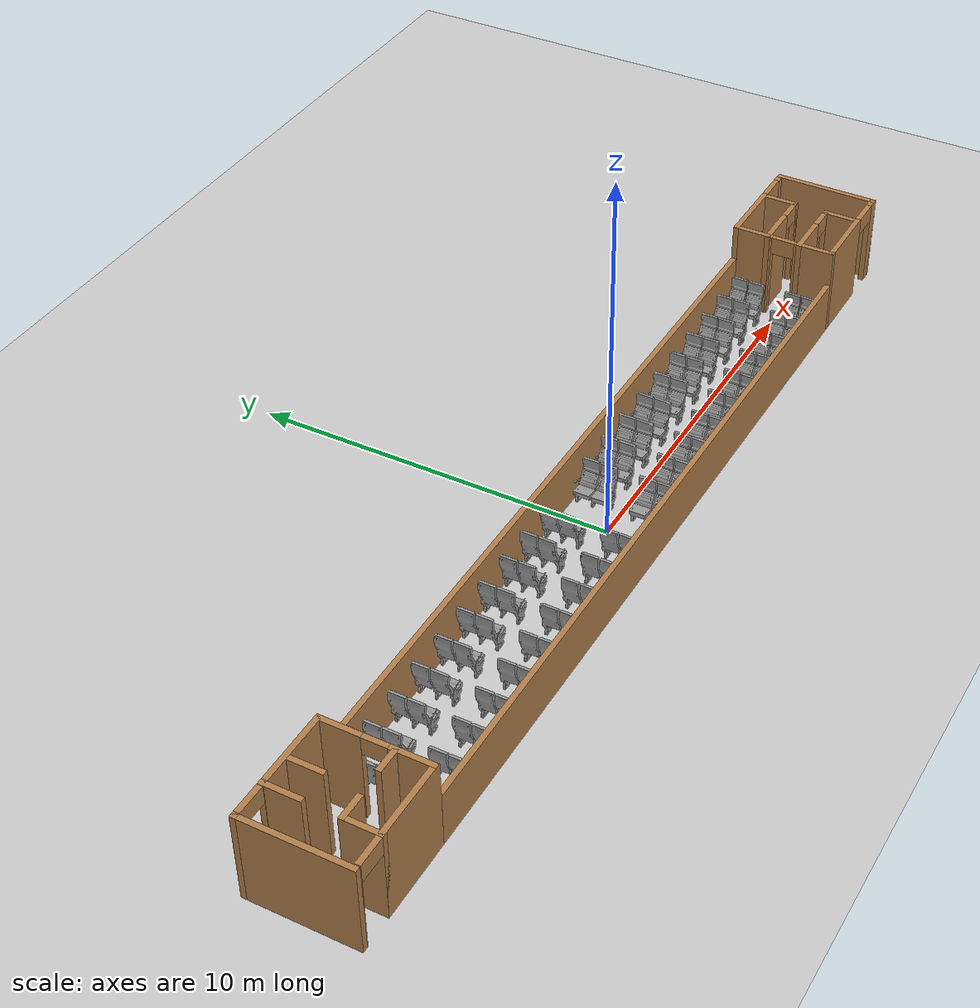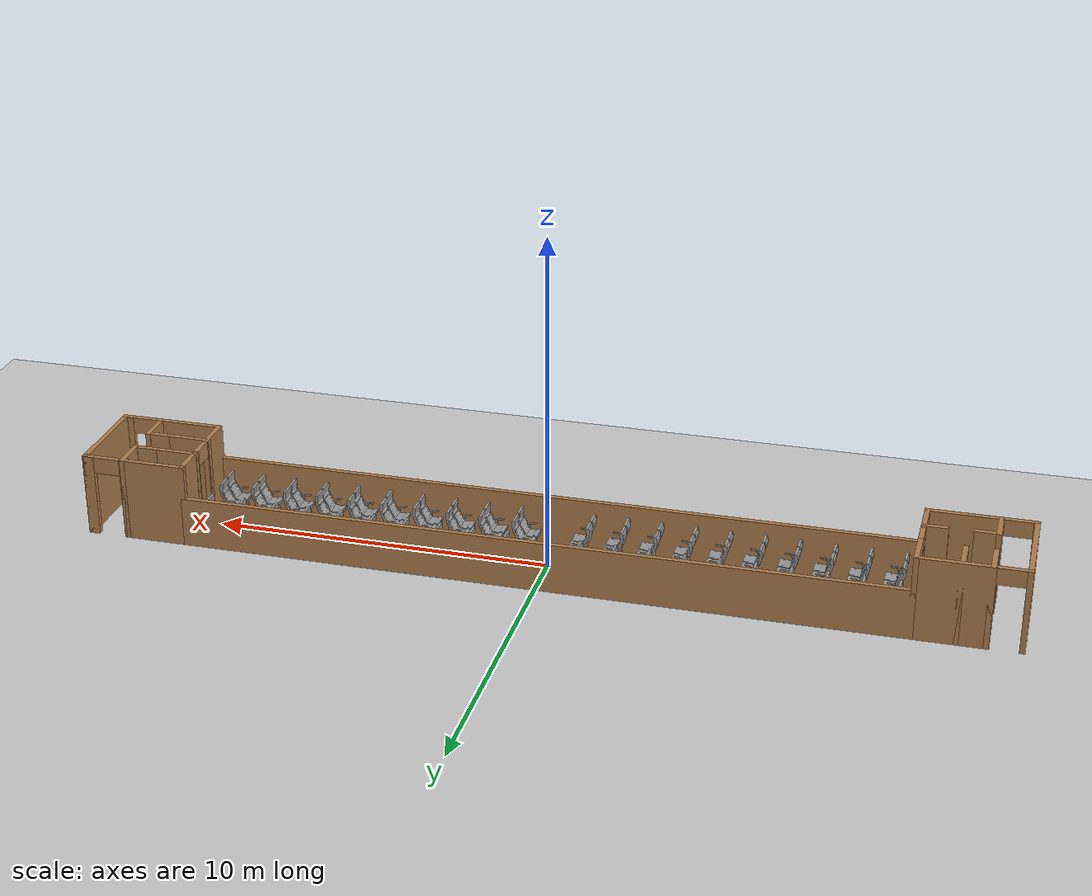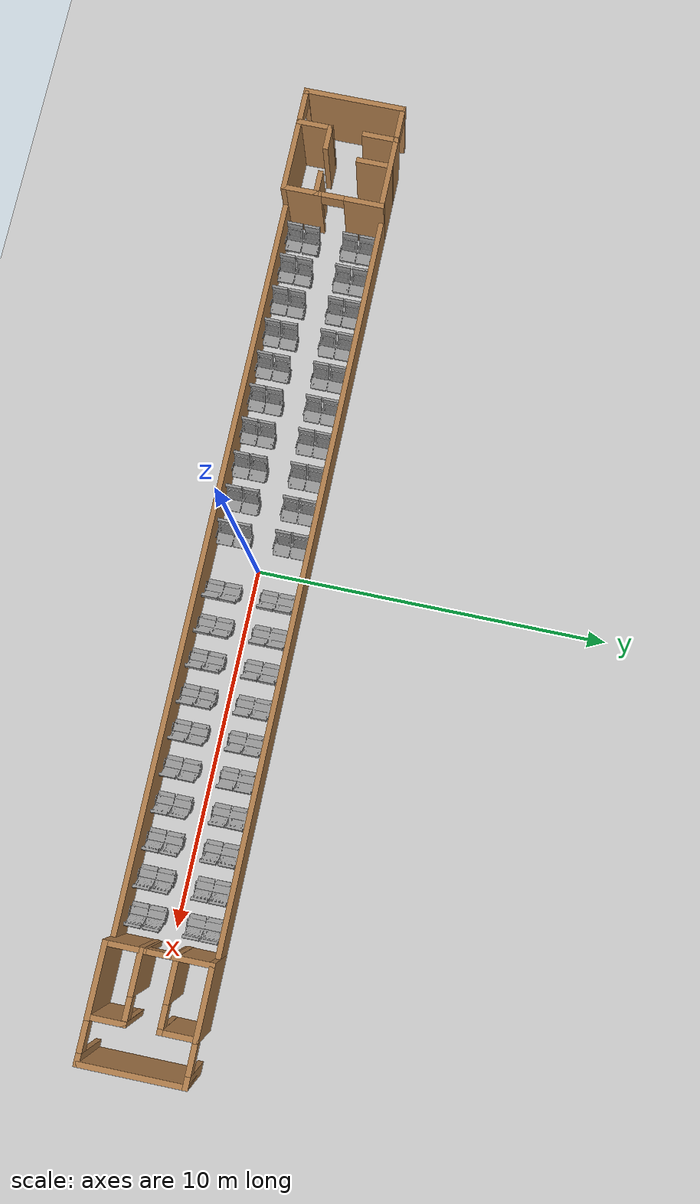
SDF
<sdf version="1.7">
 <world name="default">
  <light name="sun" type="directional">
   <pose>0 0 10 0 -0 0</pose>
   <diffuse>0.8 0.8 0.8 1</diffuse>
   <specular>0.2 0.2 0.2 1</specular>
   <attenuation>
    <range>1000</range>
    <constant>0.9</constant>
    <linear>0.01</linear>
    <quadratic>0.001</quadratic>
   </attenuation>
   <direction>-0.5 0.1 -0.9</direction>
   <spot><inner_angle>0</inner_angle><outer_angle>0</outer_angle><falloff>0</falloff></spot>
  </light>
  <model name="ground_plane">
   <static>1</static>
   <link name="link">
    <collision name="collision">
     <geometry><plane><normal>0 0 1</normal><size>100 100</size></plane></geometry>
     <surface><friction><ode><mu>100</mu><mu2>50</mu2></ode></friction></surface>
    </collision>
    <visual name="visual">
     <cast_shadows>0</cast_shadows>
     <geometry><plane><normal>0 0 1</normal><size>100 100</size></plane></geometry>
     <material>
      <script><uri>file://media/materials/scripts/gazebo.material</uri><name>Gazebo/Grey</name></script>
     </material>
    </visual>
   </link>
  </model>
  <gravity>0 0 -9.8</gravity>
  <magnetic_field>6e-06 2.3e-05 -4.2e-05</magnetic_field>
  <atmosphere type="adiabatic"/>
  <physics type="ode">
   <max_step_size>0.001</max_step_size>
   <real_time_factor>1</real_time_factor>
   <real_time_update_rate>1000</real_time_update_rate>
  </physics>
  <scene><ambient>0.4 0.4 0.4 1</ambient><background>0.7 0.7 0.7 1</background><shadows>1</shadows></scene>
  <audio><device>default</device></audio>
  <spherical_coordinates>
   <surface_model>EARTH_WGS84</surface_model>
   <latitude_deg>0</latitude_deg>
   <longitude_deg>0</longitude_deg>
   <elevation>0</elevation>
   <heading_deg>0</heading_deg>
  </spherical_coordinates>
  <model name="tejas_train">
   <pose>0.005564 0.000165 0 0 -0 0</pose>
   <link name="Wall_11">
    <pose>-10.5 0 0 0 -0 -1.5708</pose>
    <visual name="Wall_11_Visual_0">
     <pose>-0.902332 0 1.25 0 -0 0</pose>
     <geometry><box><size>1.14533 0.15 2.5</size></box></geometry>
     <material>
      <script><uri>file://media/materials/scripts/gazebo.material</uri><name>Gazebo/Wood</name></script>
      <ambient>1 1 1 1</ambient>
     </material>
     <meta><layer>0</layer></meta>
    </visual>
    <collision name="Wall_11_Collision_0">
     <geometry><box><size>1.14533 0.15 2.5</size></box></geometry>
     <pose>-0.902332 0 1.25 0 -0 0</pose>
    </collision>
    <visual name="Wall_11_Visual_1">
     <pose>0.897668 0 1.25 0 -0 0</pose>
     <geometry><box><size>1.15467 0.15 2.5</size></box></geometry>
     <material>
      <script><uri>file://media/materials/scripts/gazebo.material</uri><name>Gazebo/Wood</name></script>
      <ambient>1 1 1 1</ambient>
     </material>
     <meta><layer>0</layer></meta>
    </visual>
    <collision name="Wall_11_Collision_1">
     <geometry><box><size>1.15467 0.15 2.5</size></box></geometry>
     <pose>0.897668 0 1.25 0 -0 0</pose>
    </collision>
    <visual name="Wall_11_Visual_2">
     <pose>-0.004665 0 2.25 0 -0 0</pose>
     <geometry><box><size>0.65 0.15 0.5</size></box></geometry>
     <material>
      <script><uri>file://media/materials/scripts/gazebo.material</uri><name>Gazebo/Wood</name></script>
      <ambient>1 1 1 1</ambient>
     </material>
     <meta><layer>0</layer></meta>
    </visual>
    <collision name="Wall_11_Collision_2">
     <geometry><box><size>0.65 0.15 0.5</size></box></geometry>
     <pose>-0.004665 0 2.25 0 -0 0</pose>
    </collision>
   </link>
   <link name="Wall_13">
    <pose>10.5 0 0 0 -0 -1.5708</pose>
    <visual name="Wall_13_Visual_0">
     <pose>-0.902332 0 1.25 0 -0 0</pose>
     <geometry><box><size>1.14533 0.15 2.5</size></box></geometry>
     <material>
      <script><uri>file://media/materials/scripts/gazebo.material</uri><name>Gazebo/Wood</name></script>
      <ambient>1 1 1 1</ambient>
     </material>
     <meta><layer>0</layer></meta>
    </visual>
    <collision name="Wall_13_Collision_0">
     <geometry><box><size>1.14533 0.15 2.5</size></box></geometry>
     <pose>-0.902332 0 1.25 0 -0 0</pose>
    </collision>
    <visual name="Wall_13_Visual_1">
     <pose>0.897668 0 1.25 0 -0 0</pose>
     <geometry><box><size>1.15467 0.15 2.5</size></box></geometry>
     <material>
      <script><uri>file://media/materials/scripts/gazebo.material</uri><name>Gazebo/Wood</name></script>
      <ambient>1 1 1 1</ambient>
     </material>
     <meta><layer>0</layer></meta>
    </visual>
    <collision name="Wall_13_Collision_1">
     <geometry><box><size>1.15467 0.15 2.5</size></box></geometry>
     <pose>0.897668 0 1.25 0 -0 0</pose>
    </collision>
    <visual name="Wall_13_Visual_2">
     <pose>-0.004665 0 2.25 0 -0 0</pose>
     <geometry><box><size>0.65 0.15 0.5</size></box></geometry>
     <material>
      <script><uri>file://media/materials/scripts/gazebo.material</uri><name>Gazebo/Wood</name></script>
      <ambient>1 1 1 1</ambient>
     </material>
     <meta><layer>0</layer></meta>
    </visual>
    <collision name="Wall_13_Collision_2">
     <geometry><box><size>0.65 0.15 0.5</size></box></geometry>
     <pose>-0.004665 0 2.25 0 -0 0</pose>
    </collision>
   </link>
   <link name="Wall_15">
    <pose>-12 1.4 0 0 -0 3.14159</pose>
    <visual name="Wall_15_Visual_0">
     <pose>-0.479459 0 1.25 0 -0 0</pose>
     <geometry><box><size>2.19108 0.15 2.5</size></box></geometry>
     <material>
      <script><uri>file://media/materials/scripts/gazebo.material</uri><name>Gazebo/Wood</name></script>
      <ambient>1 1 1 1</ambient>
     </material>
     <meta><layer>0</layer></meta>
    </visual>
    <collision name="Wall_15_Collision_0">
     <geometry><box><size>2.19108 0.15 2.5</size></box></geometry>
     <pose>-0.479459 0 1.25 0 -0 0</pose>
    </collision>
    <visual name="Wall_15_Visual_1">
     <pose>1.49554 0 1.25 0 -0 0</pose>
     <geometry><box><size>0.158918 0.15 2.5</size></box></geometry>
     <material>
      <script><uri>file://media/materials/scripts/gazebo.material</uri><name>Gazebo/Wood</name></script>
      <ambient>1 1 1 1</ambient>
     </material>
     <meta><layer>0</layer></meta>
    </visual>
    <collision name="Wall_15_Collision_1">
     <geometry><box><size>0.158918 0.15 2.5</size></box></geometry>
     <pose>1.49554 0 1.25 0 -0 0</pose>
    </collision>
    <visual name="Wall_15_Visual_2">
     <pose>1.01608 0 2.25 0 -0 0</pose>
     <geometry><box><size>0.8 0.15 0.5</size></box></geometry>
     <material>
      <script><uri>file://media/materials/scripts/gazebo.material</uri><name>Gazebo/Wood</name></script>
      <ambient>1 1 1 1</ambient>
     </material>
     <meta><layer>0</layer></meta>
    </visual>
    <collision name="Wall_15_Collision_2">
     <geometry><box><size>0.8 0.15 0.5</size></box></geometry>
     <pose>1.01608 0 2.25 0 -0 0</pose>
    </collision>
   </link>
   <link name="Wall_17">
    <pose>-12 -1.4 0 0 -0 3.14159</pose>
    <visual name="Wall_17_Visual_0">
     <pose>-0.487891 0 1.25 0 -0 0</pose>
     <geometry><box><size>2.17422 0.15 2.5</size></box></geometry>
     <material>
      <script><uri>file://media/materials/scripts/gazebo.material</uri><name>Gazebo/Wood</name></script>
      <ambient>1 1 1 1</ambient>
     </material>
     <meta><layer>0</layer></meta>
    </visual>
    <collision name="Wall_17_Collision_0">
     <geometry><box><size>2.17422 0.15 2.5</size></box></geometry>
     <pose>-0.487891 0 1.25 0 -0 0</pose>
    </collision>
    <visual name="Wall_17_Visual_1">
     <pose>1.48711 0 1.25 0 -0 0</pose>
     <geometry><box><size>0.175782 0.15 2.5</size></box></geometry>
     <material>
      <script><uri>file://media/materials/scripts/gazebo.material</uri><name>Gazebo/Wood</name></script>
      <ambient>1 1 1 1</ambient>
     </material>
     <meta><layer>0</layer></meta>
    </visual>
    <collision name="Wall_17_Collision_1">
     <geometry><box><size>0.175782 0.15 2.5</size></box></geometry>
     <pose>1.48711 0 1.25 0 -0 0</pose>
    </collision>
    <visual name="Wall_17_Visual_2">
     <pose>0.999218 0 2.25 0 -0 0</pose>
     <geometry><box><size>0.8 0.15 0.5</size></box></geometry>
     <material>
      <script><uri>file://media/materials/scripts/gazebo.material</uri><name>Gazebo/Wood</name></script>
      <ambient>1 1 1 1</ambient>
     </material>
     <meta><layer>0</layer></meta>
    </visual>
    <collision name="Wall_17_Collision_2">
     <geometry><box><size>0.8 0.15 0.5</size></box></geometry>
     <pose>0.999218 0 2.25 0 -0 0</pose>
    </collision>
   </link>
   <link name="Wall_19">
    <collision name="Wall_19_Collision">
     <geometry><box><size>1.05 0.15 2.5</size></box></geometry>
     <pose>0 0 1.25 0 -0 0</pose>
    </collision>
    <visual name="Wall_19_Visual">
     <pose>0 0 1.25 0 -0 0</pose>
     <geometry><box><size>1.05 0.15 2.5</size></box></geometry>
     <material>
      <script><uri>file://media/materials/scripts/gazebo.material</uri><name>Gazebo/Wood</name></script>
      <ambient>1 1 1 1</ambient>
     </material>
     <meta><layer>0</layer></meta>
    </visual>
    <pose>-11.718 0.95 0 0 -0 -1.5708</pose>
   </link>
   <link name="Wall_21">
    <collision name="Wall_21_Collision">
     <geometry><box><size>1.05 0.15 2.5</size></box></geometry>
     <pose>0 0 1.25 0 -0 0</pose>
    </collision>
    <visual name="Wall_21_Visual">
     <pose>0 0 1.25 0 -0 0</pose>
     <geometry><box><size>1.05 0.15 2.5</size></box></geometry>
     <material>
      <script><uri>file://media/materials/scripts/gazebo.material</uri><name>Gazebo/Wood</name></script>
      <ambient>1 1 1 1</ambient>
     </material>
     <meta><layer>0</layer></meta>
    </visual>
    <pose>-12.527 -0.95 0 0 -0 1.5708</pose>
   </link>
   <link name="Wall_23">
    <collision name="Wall_23_Collision">
     <geometry><box><size>1.05 0.15 2.5</size></box></geometry>
     <pose>0 0 1.25 0 -0 0</pose>
    </collision>
    <visual name="Wall_23_Visual">
     <pose>0 0 1.25 0 -0 0</pose>
     <geometry><box><size>1.05 0.15 2.5</size></box></geometry>
     <material>
      <script><uri>file://media/materials/scripts/gazebo.material</uri><name>Gazebo/Wood</name></script>
      <ambient>1 1 1 1</ambient>
     </material>
     <meta><layer>0</layer></meta>
    </visual>
    <pose>-12.527 0.95 0 0 -0 -1.5708</pose>
   </link>
   <link name="Wall_27">
    <collision name="Wall_27_Collision">
     <geometry><box><size>0.75 0.15 2.5</size></box></geometry>
     <pose>0 0 1.25 0 -0 0</pose>
    </collision>
    <visual name="Wall_27_Visual">
     <pose>0 0 1.25 0 -0 0</pose>
     <geometry><box><size>0.75 0.15 2.5</size></box></geometry>
     <material>
      <script><uri>file://media/materials/scripts/gazebo.material</uri><name>Gazebo/Wood</name></script>
      <ambient>1 1 1 1</ambient>
     </material>
     <meta><layer>0</layer></meta>
    </visual>
    <pose>-12.227 -0.5 0 0 -0 0</pose>
   </link>
   <link name="Wall_29">
    <collision name="Wall_29_Collision">
     <geometry><box><size>0.75 0.15 2.5</size></box></geometry>
     <pose>0 0 1.25 0 -0 0</pose>
    </collision>
    <visual name="Wall_29_Visual">
     <pose>0 0 1.25 0 -0 0</pose>
     <geometry><box><size>0.75 0.15 2.5</size></box></geometry>
     <material>
      <script><uri>file://media/materials/scripts/gazebo.material</uri><name>Gazebo/Wood</name></script>
      <ambient>1 1 1 1</ambient>
     </material>
     <meta><layer>0</layer></meta>
    </visual>
    <pose>-10.8034 -0.478648 0 0 -0 3.14159</pose>
   </link>
   <link name="Wall_31">
    <collision name="Wall_31_Collision">
     <geometry><box><size>2.95 0.15 2.5</size></box></geometry>
     <pose>0 0 1.25 0 -0 0</pose>
    </collision>
    <visual name="Wall_31_Visual">
     <pose>0 0 1.25 0 -0 0</pose>
     <geometry><box><size>2.95 0.15 2.5</size></box></geometry>
     <material>
      <script><uri>file://media/materials/scripts/gazebo.material</uri><name>Gazebo/Wood</name></script>
      <ambient>1 1 1 1</ambient>
     </material>
     <meta><layer>0</layer></meta>
    </visual>
    <pose>-13.5 0 0 0 -0 -1.5708</pose>
   </link>
   <link name="Wall_35">
    <pose>12 1.4 0 0 -0 0</pose>
    <visual name="Wall_35_Visual_0">
     <pose>-0.569532 0 1.25 0 -0 0</pose>
     <geometry><box><size>2.01094 0.15 2.5</size></box></geometry>
     <material>
      <script><uri>file://media/materials/scripts/gazebo.material</uri><name>Gazebo/Wood</name></script>
      <ambient>1 1 1 1</ambient>
     </material>
     <meta><layer>0</layer></meta>
    </visual>
    <collision name="Wall_35_Collision_0">
     <geometry><box><size>2.01094 0.15 2.5</size></box></geometry>
     <pose>-0.569532 0 1.25 0 -0 0</pose>
    </collision>
    <visual name="Wall_35_Visual_1">
     <pose>1.40547 0 1.25 0 -0 0</pose>
     <geometry><box><size>0.339064 0.15 2.5</size></box></geometry>
     <material>
      <script><uri>file://media/materials/scripts/gazebo.material</uri><name>Gazebo/Wood</name></script>
      <ambient>1 1 1 1</ambient>
     </material>
     <meta><layer>0</layer></meta>
    </visual>
    <collision name="Wall_35_Collision_1">
     <geometry><box><size>0.339064 0.15 2.5</size></box></geometry>
     <pose>1.40547 0 1.25 0 -0 0</pose>
    </collision>
    <visual name="Wall_35_Visual_2">
     <pose>0.835936 0 2.25 0 -0 0</pose>
     <geometry><box><size>0.8 0.15 0.5</size></box></geometry>
     <material>
      <script><uri>file://media/materials/scripts/gazebo.material</uri><name>Gazebo/Wood</name></script>
      <ambient>1 1 1 1</ambient>
     </material>
     <meta><layer>0</layer></meta>
    </visual>
    <collision name="Wall_35_Collision_2">
     <geometry><box><size>0.8 0.15 0.5</size></box></geometry>
     <pose>0.835936 0 2.25 0 -0 0</pose>
    </collision>
   </link>
   <link name="Wall_37">
    <pose>12 -1.4 0 0 -0 0</pose>
    <visual name="Wall_37_Visual_0">
     <pose>-0.569532 0 1.25 0 -0 0</pose>
     <geometry><box><size>2.01094 0.15 2.5</size></box></geometry>
     <material>
      <script><uri>file://media/materials/scripts/gazebo.material</uri><name>Gazebo/Wood</name></script>
      <ambient>1 1 1 1</ambient>
     </material>
     <meta><layer>0</layer></meta>
    </visual>
    <collision name="Wall_37_Collision_0">
     <geometry><box><size>2.01094 0.15 2.5</size></box></geometry>
     <pose>-0.569532 0 1.25 0 -0 0</pose>
    </collision>
    <visual name="Wall_37_Visual_1">
     <pose>1.40547 0 1.25 0 -0 0</pose>
     <geometry><box><size>0.339064 0.15 2.5</size></box></geometry>
     <material>
      <script><uri>file://media/materials/scripts/gazebo.material</uri><name>Gazebo/Wood</name></script>
      <ambient>1 1 1 1</ambient>
     </material>
     <meta><layer>0</layer></meta>
    </visual>
    <collision name="Wall_37_Collision_1">
     <geometry><box><size>0.339064 0.15 2.5</size></box></geometry>
     <pose>1.40547 0 1.25 0 -0 0</pose>
    </collision>
    <visual name="Wall_37_Visual_2">
     <pose>0.835936 0 2.25 0 -0 0</pose>
     <geometry><box><size>0.8 0.15 0.5</size></box></geometry>
     <material>
      <script><uri>file://media/materials/scripts/gazebo.material</uri><name>Gazebo/Wood</name></script>
      <ambient>1 1 1 1</ambient>
     </material>
     <meta><layer>0</layer></meta>
    </visual>
    <collision name="Wall_37_Collision_2">
     <geometry><box><size>0.8 0.15 0.5</size></box></geometry>
     <pose>0.835936 0 2.25 0 -0 0</pose>
    </collision>
   </link>
   <link name="Wall_39">
    <pose>11.417 0.466 0 0 -0 0</pose>
    <visual name="Wall_39_Visual_0">
     <pose>-0.378988 0 1.25 0 -0 0</pose>
     <geometry><box><size>1.24202 0.15 2.5</size></box></geometry>
     <material>
      <script><uri>file://media/materials/scripts/gazebo.material</uri><name>Gazebo/Wood</name></script>
      <ambient>1 1 1 1</ambient>
     </material>
     <meta><layer>0</layer></meta>
    </visual>
    <collision name="Wall_39_Collision_0">
     <geometry><box><size>1.24202 0.15 2.5</size></box></geometry>
     <pose>-0.378988 0 1.25 0 -0 0</pose>
    </collision>
    <visual name="Wall_39_Visual_1">
     <pose>0.921012 0 1.25 0 -0 0</pose>
     <geometry><box><size>0.157975 0.15 2.5</size></box></geometry>
     <material>
      <script><uri>file://media/materials/scripts/gazebo.material</uri><name>Gazebo/Wood</name></script>
      <ambient>1 1 1 1</ambient>
     </material>
     <meta><layer>0</layer></meta>
    </visual>
    <collision name="Wall_39_Collision_1">
     <geometry><box><size>0.157975 0.15 2.5</size></box></geometry>
     <pose>0.921012 0 1.25 0 -0 0</pose>
    </collision>
    <visual name="Wall_39_Visual_2">
     <pose>0.542025 0 2.25 0 -0 0</pose>
     <geometry><box><size>0.6 0.15 0.5</size></box></geometry>
     <material>
      <script><uri>file://media/materials/scripts/gazebo.material</uri><name>Gazebo/Wood</name></script>
      <ambient>1 1 1 1</ambient>
     </material>
     <meta><layer>0</layer></meta>
    </visual>
    <collision name="Wall_39_Collision_2">
     <geometry><box><size>0.6 0.15 0.5</size></box></geometry>
     <pose>0.542025 0 2.25 0 -0 0</pose>
    </collision>
   </link>
   <link name="Wall_40">
    <collision name="Wall_40_Collision">
     <geometry><box><size>1.084 0.15 2.5</size></box></geometry>
     <pose>0 0 1.25 0 -0 0</pose>
    </collision>
    <visual name="Wall_40_Visual">
     <pose>0 0 1.25 0 -0 0</pose>
     <geometry><box><size>1.084 0.15 2.5</size></box></geometry>
     <material>
      <script><uri>file://media/materials/scripts/gazebo.material</uri><name>Gazebo/Wood</name></script>
      <ambient>1 1 1 1</ambient>
     </material>
     <meta><layer>0</layer></meta>
    </visual>
    <pose>12.342 0.933 0 0 -0 1.5708</pose>
   </link>
   <link name="Wall_42">
    <pose>11.417 -0.466 0 0 -0 0</pose>
    <visual name="Wall_42_Visual_0">
     <pose>-0.378988 0 1.25 0 -0 0</pose>
     <geometry><box><size>1.24202 0.15 2.5</size></box></geometry>
     <material>
      <script><uri>file://media/materials/scripts/gazebo.material</uri><name>Gazebo/Wood</name></script>
      <ambient>1 1 1 1</ambient>
     </material>
     <meta><layer>0</layer></meta>
    </visual>
    <collision name="Wall_42_Collision_0">
     <geometry><box><size>1.24202 0.15 2.5</size></box></geometry>
     <pose>-0.378988 0 1.25 0 -0 0</pose>
    </collision>
    <visual name="Wall_42_Visual_1">
     <pose>0.921012 0 1.25 0 -0 0</pose>
     <geometry><box><size>0.157975 0.15 2.5</size></box></geometry>
     <material>
      <script><uri>file://media/materials/scripts/gazebo.material</uri><name>Gazebo/Wood</name></script>
      <ambient>1 1 1 1</ambient>
     </material>
     <meta><layer>0</layer></meta>
    </visual>
    <collision name="Wall_42_Collision_1">
     <geometry><box><size>0.157975 0.15 2.5</size></box></geometry>
     <pose>0.921012 0 1.25 0 -0 0</pose>
    </collision>
    <visual name="Wall_42_Visual_2">
     <pose>0.542025 0 2.25 0 -0 0</pose>
     <geometry><box><size>0.6 0.15 0.5</size></box></geometry>
     <material>
      <script><uri>file://media/materials/scripts/gazebo.material</uri><name>Gazebo/Wood</name></script>
      <ambient>1 1 1 1</ambient>
     </material>
     <meta><layer>0</layer></meta>
    </visual>
    <collision name="Wall_42_Collision_2">
     <geometry><box><size>0.6 0.15 0.5</size></box></geometry>
     <pose>0.542025 0 2.25 0 -0 0</pose>
    </collision>
   </link>
   <link name="Wall_43">
    <collision name="Wall_43_Collision">
     <geometry><box><size>1.08072 0.15 2.5</size></box></geometry>
     <pose>0 0 1.25 0 -0 0</pose>
    </collision>
    <visual name="Wall_43_Visual">
     <pose>0 0 1.25 0 -0 0</pose>
     <geometry><box><size>1.08072 0.15 2.5</size></box></geometry>
     <material>
      <script><uri>file://media/materials/scripts/gazebo.material</uri><name>Gazebo/Wood</name></script>
      <ambient>1 1 1 1</ambient>
     </material>
     <meta><layer>0</layer></meta>
    </visual>
    <pose>12.342 -0.931 0 0 -0 -1.5708</pose>
   </link>
   <link name="Wall_45">
    <collision name="Wall_45_Collision">
     <geometry><box><size>2.95 0.15 2.5</size></box></geometry>
     <pose>0 0 1.25 0 -0 0</pose>
    </collision>
    <visual name="Wall_45_Visual">
     <pose>0 0 1.25 0 -0 0</pose>
     <geometry><box><size>2.95 0.15 2.5</size></box></geometry>
     <material>
      <script><uri>file://media/materials/scripts/gazebo.material</uri><name>Gazebo/Wood</name></script>
      <ambient>1 1 1 1</ambient>
     </material>
     <meta><layer>0</layer></meta>
    </visual>
    <pose>13.5 0 0 0 -0 -1.5708</pose>
   </link>
   <link name="Wall_7">
    <collision name="Wall_7_Collision">
     <geometry><box><size>21.15 0.15 1.5</size></box></geometry>
     <pose>0 0 0.75 0 -0 0</pose>
    </collision>
    <visual name="Wall_7_Visual">
     <pose>0 0 0.75 0 -0 0</pose>
     <geometry><box><size>21.15 0.15 1.5</size></box></geometry>
     <material>
      <script><uri>file://media/materials/scripts/gazebo.material</uri><name>Gazebo/Wood</name></script>
      <ambient>1 1 1 1</ambient>
     </material>
     <meta><layer>0</layer></meta>
    </visual>
    <pose>0 1.4 0 0 -0 0</pose>
   </link>
   <link name="Wall_9">
    <collision name="Wall_9_Collision">
     <geometry><box><size>21.15 0.15 1.5</size></box></geometry>
     <pose>0 0 0.75 0 -0 0</pose>
    </collision>
    <visual name="Wall_9_Visual">
     <pose>0 0 0.75 0 -0 0</pose>
     <geometry><box><size>21.15 0.15 1.5</size></box></geometry>
     <material>
      <script><uri>file://media/materials/scripts/gazebo.material</uri><name>Gazebo/Wood</name></script>
      <ambient>1 1 1 1</ambient>
     </material>
     <meta><layer>0</layer></meta>
    </visual>
    <pose>0 -1.4 0 0 -0 0</pose>
   </link>
   <static>1</static>
  </model>
  <model name="seat_10">
   <model name="seat">
    <link name="link_0">
     <inertial>
      <mass>1</mass>
      <inertia>
       <ixx>0.166667</ixx>
       <ixy>0</ixy>
       <ixz>0</ixz>
       <iyy>0.166667</iyy>
       <iyz>0</iyz>
       <izz>0.166667</izz>
      </inertia>
     </inertial>
     <visual name="visual">
      <pose>-0.3 -0.5 0 0 -0 0</pose>
      <geometry><mesh><uri>model://seat1/meshes/seat1.stl</uri><scale>0.001 0.001 0.001</scale></mesh></geometry>
      <material>
       <lighting>1</lighting>
       <script><uri>file://media/materials/scripts/gazebo.material</uri><name>Gazebo/Grey</name></script>
       <shader type="pixel"><normal_map>__default__</normal_map></shader>
       <ambient>0.3 0.3 0.3 1</ambient>
       <diffuse>0.7 0.7 0.7 1</diffuse>
       <specular>0.01 0.01 0.01 1</specular>
       <emissive>0 0 0 1</emissive>
      </material>
     </visual>
     <collision name="collision">
      <pose>-0.3 -0.5 0 0 -0 0</pose>
      <geometry><mesh><uri>model://seat1/meshes/seat1.stl</uri><scale>0.001 0.001 0.001</scale></mesh></geometry>
      <surface>
       <friction>
        <ode><mu>10000</mu><mu2>10000</mu2><fdir1>0 0 0</fdir1><slip1>0</slip1><slip2>0</slip2></ode>
        <torsional>
         <coefficient>1</coefficient>
         <patch_radius>0</patch_radius>
         <surface_radius>0</surface_radius>
         <use_patch_radius>1</use_patch_radius>
         <ode><slip>0</slip></ode>
        </torsional>
       </friction>
       <bounce><restitution_coefficient>0</restitution_coefficient><threshold>1e+06</threshold></bounce>
       <contact>
        <collide_without_contact>0</collide_without_contact>
        <collide_without_contact_bitmask>1</collide_without_contact_bitmask>
        <collide_bitmask>1</collide_bitmask>
        <ode>
         <soft_cfm>0</soft_cfm>
         <soft_erp>0.2</soft_erp>
         <kp>1e+13</kp>
         <kd>1</kd>
         <max_vel>0.01</max_vel>
         <min_depth>0</min_depth>
        </ode>
        <bullet>
         <split_impulse>1</split_impulse>
         <split_impulse_penetration_threshold>-0.01</split_impulse_penetration_threshold>
         <soft_cfm>0</soft_cfm>
         <soft_erp>0.2</soft_erp>
         <kp>1e+13</kp>
         <kd>1</kd>
        </bullet>
       </contact>
      </surface>
     </collision>
    </link>
    <static>0</static>
    <pose>-4.49906 0.001451 0 0 -0 0</pose>
   </model>
   <model name="seat_0">
    <link name="link_0">
     <inertial>
      <mass>1</mass>
      <inertia>
       <ixx>0.166667</ixx>
       <ixy>0</ixy>
       <ixz>0</ixz>
       <iyy>0.166667</iyy>
       <iyz>0</iyz>
       <izz>0.166667</izz>
      </inertia>
     </inertial>
     <visual name="visual">
      <pose>-0.3 -0.5 0 0 -0 0</pose>
      <geometry><mesh><uri>model://seat1/meshes/seat1.stl</uri><scale>0.001 0.001 0.001</scale></mesh></geometry>
      <material>
       <lighting>1</lighting>
       <script><uri>file://media/materials/scripts/gazebo.material</uri><name>Gazebo/Grey</name></script>
       <shader type="pixel"><normal_map>__default__</normal_map></shader>
       <ambient>0.3 0.3 0.3 1</ambient>
       <diffuse>0.7 0.7 0.7 1</diffuse>
       <specular>0.01 0.01 0.01 1</specular>
       <emissive>0 0 0 1</emissive>
      </material>
     </visual>
     <collision name="collision">
      <pose>-0.3 -0.5 0 0 -0 0</pose>
      <geometry><mesh><uri>model://seat1/meshes/seat1.stl</uri><scale>0.001 0.001 0.001</scale></mesh></geometry>
      <surface>
       <friction>
        <ode><mu>10000</mu><mu2>10000</mu2><fdir1>0 0 0</fdir1><slip1>0</slip1><slip2>0</slip2></ode>
        <torsional>
         <coefficient>1</coefficient>
         <patch_radius>0</patch_radius>
         <surface_radius>0</surface_radius>
         <use_patch_radius>1</use_patch_radius>
         <ode><slip>0</slip></ode>
        </torsional>
       </friction>
       <bounce><restitution_coefficient>0</restitution_coefficient><threshold>1e+06</threshold></bounce>
       <contact>
        <collide_without_contact>0</collide_without_contact>
        <collide_without_contact_bitmask>1</collide_without_contact_bitmask>
        <collide_bitmask>1</collide_bitmask>
        <ode>
         <soft_cfm>0</soft_cfm>
         <soft_erp>0.2</soft_erp>
         <kp>1e+13</kp>
         <kd>1</kd>
         <max_vel>0.01</max_vel>
         <min_depth>0</min_depth>
        </ode>
        <bullet>
         <split_impulse>1</split_impulse>
         <split_impulse_penetration_threshold>-0.01</split_impulse_penetration_threshold>
         <soft_cfm>0</soft_cfm>
         <soft_erp>0.2</soft_erp>
         <kp>1e+13</kp>
         <kd>1</kd>
        </bullet>
       </contact>
      </surface>
     </collision>
    </link>
    <static>0</static>
    <pose>-3.50213 0.000104 0 0 -0 0</pose>
   </model>
   <model name="seat_1">
    <link name="link_0">
     <inertial>
      <mass>1</mass>
      <inertia>
       <ixx>0.166667</ixx>
       <ixy>0</ixy>
       <ixz>0</ixz>
       <iyy>0.166667</iyy>
       <iyz>0</iyz>
       <izz>0.166667</izz>
      </inertia>
     </inertial>
     <visual name="visual">
      <pose>-0.3 -0.5 0 0 -0 0</pose>
      <geometry><mesh><uri>model://seat1/meshes/seat1.stl</uri><scale>0.001 0.001 0.001</scale></mesh></geometry>
      <material>
       <lighting>1</lighting>
       <script><uri>file://media/materials/scripts/gazebo.material</uri><name>Gazebo/Grey</name></script>
       <shader type="pixel"><normal_map>__default__</normal_map></shader>
       <ambient>0.3 0.3 0.3 1</ambient>
       <diffuse>0.7 0.7 0.7 1</diffuse>
       <specular>0.01 0.01 0.01 1</specular>
       <emissive>0 0 0 1</emissive>
      </material>
     </visual>
     <collision name="collision">
      <pose>-0.3 -0.5 0 0 -0 0</pose>
      <geometry><mesh><uri>model://seat1/meshes/seat1.stl</uri><scale>0.001 0.001 0.001</scale></mesh></geometry>
      <surface>
       <friction>
        <ode><mu>10000</mu><mu2>10000</mu2><fdir1>0 0 0</fdir1><slip1>0</slip1><slip2>0</slip2></ode>
        <torsional>
         <coefficient>1</coefficient>
         <patch_radius>0</patch_radius>
         <surface_radius>0</surface_radius>
         <use_patch_radius>1</use_patch_radius>
         <ode><slip>0</slip></ode>
        </torsional>
       </friction>
       <bounce><restitution_coefficient>0</restitution_coefficient><threshold>1e+06</threshold></bounce>
       <contact>
        <collide_without_contact>0</collide_without_contact>
        <collide_without_contact_bitmask>1</collide_without_contact_bitmask>
        <collide_bitmask>1</collide_bitmask>
        <ode>
         <soft_cfm>0</soft_cfm>
         <soft_erp>0.2</soft_erp>
         <kp>1e+13</kp>
         <kd>1</kd>
         <max_vel>0.01</max_vel>
         <min_depth>0</min_depth>
        </ode>
        <bullet>
         <split_impulse>1</split_impulse>
         <split_impulse_penetration_threshold>-0.01</split_impulse_penetration_threshold>
         <soft_cfm>0</soft_cfm>
         <soft_erp>0.2</soft_erp>
         <kp>1e+13</kp>
         <kd>1</kd>
        </bullet>
       </contact>
      </surface>
     </collision>
    </link>
    <static>0</static>
    <pose>-2.50166 -0.002281 0 0 -0 0</pose>
   </model>
   <model name="seat_2">
    <link name="link_0">
     <inertial>
      <mass>1</mass>
      <inertia>
       <ixx>0.166667</ixx>
       <ixy>0</ixy>
       <ixz>0</ixz>
       <iyy>0.166667</iyy>
       <iyz>0</iyz>
       <izz>0.166667</izz>
      </inertia>
     </inertial>
     <visual name="visual">
      <pose>-0.3 -0.5 0 0 -0 0</pose>
      <geometry><mesh><uri>model://seat1/meshes/seat1.stl</uri><scale>0.001 0.001 0.001</scale></mesh></geometry>
      <material>
       <lighting>1</lighting>
       <script><uri>file://media/materials/scripts/gazebo.material</uri><name>Gazebo/Grey</name></script>
       <shader type="pixel"><normal_map>__default__</normal_map></shader>
       <ambient>0.3 0.3 0.3 1</ambient>
       <diffuse>0.7 0.7 0.7 1</diffuse>
       <specular>0.01 0.01 0.01 1</specular>
       <emissive>0 0 0 1</emissive>
      </material>
     </visual>
     <collision name="collision">
      <pose>-0.3 -0.5 0 0 -0 0</pose>
      <geometry><mesh><uri>model://seat1/meshes/seat1.stl</uri><scale>0.001 0.001 0.001</scale></mesh></geometry>
      <surface>
       <friction>
        <ode><mu>10000</mu><mu2>10000</mu2><fdir1>0 0 0</fdir1><slip1>0</slip1><slip2>0</slip2></ode>
        <torsional>
         <coefficient>1</coefficient>
         <patch_radius>0</patch_radius>
         <surface_radius>0</surface_radius>
         <use_patch_radius>1</use_patch_radius>
         <ode><slip>0</slip></ode>
        </torsional>
       </friction>
       <bounce><restitution_coefficient>0</restitution_coefficient><threshold>1e+06</threshold></bounce>
       <contact>
        <collide_without_contact>0</collide_without_contact>
        <collide_without_contact_bitmask>1</collide_without_contact_bitmask>
        <collide_bitmask>1</collide_bitmask>
        <ode>
         <soft_cfm>0</soft_cfm>
         <soft_erp>0.2</soft_erp>
         <kp>1e+13</kp>
         <kd>1</kd>
         <max_vel>0.01</max_vel>
         <min_depth>0</min_depth>
        </ode>
        <bullet>
         <split_impulse>1</split_impulse>
         <split_impulse_penetration_threshold>-0.01</split_impulse_penetration_threshold>
         <soft_cfm>0</soft_cfm>
         <soft_erp>0.2</soft_erp>
         <kp>1e+13</kp>
         <kd>1</kd>
        </bullet>
       </contact>
      </surface>
     </collision>
    </link>
    <static>0</static>
    <pose>-1.49886 -0.001439 0 0 -0 0</pose>
   </model>
   <model name="seat_3">
    <link name="link_0">
     <inertial>
      <mass>1</mass>
      <inertia>
       <ixx>0.166667</ixx>
       <ixy>0</ixy>
       <ixz>0</ixz>
       <iyy>0.166667</iyy>
       <iyz>0</iyz>
       <izz>0.166667</izz>
      </inertia>
     </inertial>
     <visual name="visual">
      <pose>-0.3 -0.5 0 0 -0 0</pose>
      <geometry><mesh><uri>model://seat1/meshes/seat1.stl</uri><scale>0.001 0.001 0.001</scale></mesh></geometry>
      <material>
       <lighting>1</lighting>
       <script><uri>file://media/materials/scripts/gazebo.material</uri><name>Gazebo/Grey</name></script>
       <shader type="pixel"><normal_map>__default__</normal_map></shader>
       <ambient>0.3 0.3 0.3 1</ambient>
       <diffuse>0.7 0.7 0.7 1</diffuse>
       <specular>0.01 0.01 0.01 1</specular>
       <emissive>0 0 0 1</emissive>
      </material>
     </visual>
     <collision name="collision">
      <pose>-0.3 -0.5 0 0 -0 0</pose>
      <geometry><mesh><uri>model://seat1/meshes/seat1.stl</uri><scale>0.001 0.001 0.001</scale></mesh></geometry>
      <surface>
       <friction>
        <ode><mu>10000</mu><mu2>10000</mu2><fdir1>0 0 0</fdir1><slip1>0</slip1><slip2>0</slip2></ode>
        <torsional>
         <coefficient>1</coefficient>
         <patch_radius>0</patch_radius>
         <surface_radius>0</surface_radius>
         <use_patch_radius>1</use_patch_radius>
         <ode><slip>0</slip></ode>
        </torsional>
       </friction>
       <bounce><restitution_coefficient>0</restitution_coefficient><threshold>1e+06</threshold></bounce>
       <contact>
        <collide_without_contact>0</collide_without_contact>
        <collide_without_contact_bitmask>1</collide_without_contact_bitmask>
        <collide_bitmask>1</collide_bitmask>
        <ode>
         <soft_cfm>0</soft_cfm>
         <soft_erp>0.2</soft_erp>
         <kp>1e+13</kp>
         <kd>1</kd>
         <max_vel>0.01</max_vel>
         <min_depth>0</min_depth>
        </ode>
        <bullet>
         <split_impulse>1</split_impulse>
         <split_impulse_penetration_threshold>-0.01</split_impulse_penetration_threshold>
         <soft_cfm>0</soft_cfm>
         <soft_erp>0.2</soft_erp>
         <kp>1e+13</kp>
         <kd>1</kd>
        </bullet>
       </contact>
      </surface>
     </collision>
    </link>
    <static>0</static>
    <pose>-0.502503 -0.001106 0 0 -0 0</pose>
   </model>
   <model name="seat_4">
    <link name="link_0">
     <inertial>
      <mass>1</mass>
      <inertia>
       <ixx>0.166667</ixx>
       <ixy>0</ixy>
       <ixz>0</ixz>
       <iyy>0.166667</iyy>
       <iyz>0</iyz>
       <izz>0.166667</izz>
      </inertia>
     </inertial>
     <visual name="visual">
      <pose>-0.3 -0.5 0 0 -0 0</pose>
      <geometry><mesh><uri>model://seat1/meshes/seat1.stl</uri><scale>0.001 0.001 0.001</scale></mesh></geometry>
      <material>
       <lighting>1</lighting>
       <script><uri>file://media/materials/scripts/gazebo.material</uri><name>Gazebo/Grey</name></script>
       <shader type="pixel"><normal_map>__default__</normal_map></shader>
       <ambient>0.3 0.3 0.3 1</ambient>
       <diffuse>0.7 0.7 0.7 1</diffuse>
       <specular>0.01 0.01 0.01 1</specular>
       <emissive>0 0 0 1</emissive>
      </material>
     </visual>
     <collision name="collision">
      <pose>-0.3 -0.5 0 0 -0 0</pose>
      <geometry><mesh><uri>model://seat1/meshes/seat1.stl</uri><scale>0.001 0.001 0.001</scale></mesh></geometry>
      <surface>
       <friction>
        <ode><mu>10000</mu><mu2>10000</mu2><fdir1>0 0 0</fdir1><slip1>0</slip1><slip2>0</slip2></ode>
        <torsional>
         <coefficient>1</coefficient>
         <patch_radius>0</patch_radius>
         <surface_radius>0</surface_radius>
         <use_patch_radius>1</use_patch_radius>
         <ode><slip>0</slip></ode>
        </torsional>
       </friction>
       <bounce><restitution_coefficient>0</restitution_coefficient><threshold>1e+06</threshold></bounce>
       <contact>
        <collide_without_contact>0</collide_without_contact>
        <collide_without_contact_bitmask>1</collide_without_contact_bitmask>
        <collide_bitmask>1</collide_bitmask>
        <ode>
         <soft_cfm>0</soft_cfm>
         <soft_erp>0.2</soft_erp>
         <kp>1e+13</kp>
         <kd>1</kd>
         <max_vel>0.01</max_vel>
         <min_depth>0</min_depth>
        </ode>
        <bullet>
         <split_impulse>1</split_impulse>
         <split_impulse_penetration_threshold>-0.01</split_impulse_penetration_threshold>
         <soft_cfm>0</soft_cfm>
         <soft_erp>0.2</soft_erp>
         <kp>1e+13</kp>
         <kd>1</kd>
        </bullet>
       </contact>
      </surface>
     </collision>
    </link>
    <static>0</static>
    <pose>0.499248 0.004347 0 0 -0 0</pose>
   </model>
   <model name="seat_5">
    <link name="link_0">
     <inertial>
      <mass>1</mass>
      <inertia>
       <ixx>0.166667</ixx>
       <ixy>0</ixy>
       <ixz>0</ixz>
       <iyy>0.166667</iyy>
       <iyz>0</iyz>
       <izz>0.166667</izz>
      </inertia>
     </inertial>
     <visual name="visual">
      <pose>-0.3 -0.5 0 0 -0 0</pose>
      <geometry><mesh><uri>model://seat1/meshes/seat1.stl</uri><scale>0.001 0.001 0.001</scale></mesh></geometry>
      <material>
       <lighting>1</lighting>
       <script><uri>file://media/materials/scripts/gazebo.material</uri><name>Gazebo/Grey</name></script>
       <shader type="pixel"><normal_map>__default__</normal_map></shader>
       <ambient>0.3 0.3 0.3 1</ambient>
       <diffuse>0.7 0.7 0.7 1</diffuse>
       <specular>0.01 0.01 0.01 1</specular>
       <emissive>0 0 0 1</emissive>
      </material>
     </visual>
     <collision name="collision">
      <pose>-0.3 -0.5 0 0 -0 0</pose>
      <geometry><mesh><uri>model://seat1/meshes/seat1.stl</uri><scale>0.001 0.001 0.001</scale></mesh></geometry>
      <surface>
       <friction>
        <ode><mu>10000</mu><mu2>10000</mu2><fdir1>0 0 0</fdir1><slip1>0</slip1><slip2>0</slip2></ode>
        <torsional>
         <coefficient>1</coefficient>
         <patch_radius>0</patch_radius>
         <surface_radius>0</surface_radius>
         <use_patch_radius>1</use_patch_radius>
         <ode><slip>0</slip></ode>
        </torsional>
       </friction>
       <bounce><restitution_coefficient>0</restitution_coefficient><threshold>1e+06</threshold></bounce>
       <contact>
        <collide_without_contact>0</collide_without_contact>
        <collide_without_contact_bitmask>1</collide_without_contact_bitmask>
        <collide_bitmask>1</collide_bitmask>
        <ode>
         <soft_cfm>0</soft_cfm>
         <soft_erp>0.2</soft_erp>
         <kp>1e+13</kp>
         <kd>1</kd>
         <max_vel>0.01</max_vel>
         <min_depth>0</min_depth>
        </ode>
        <bullet>
         <split_impulse>1</split_impulse>
         <split_impulse_penetration_threshold>-0.01</split_impulse_penetration_threshold>
         <soft_cfm>0</soft_cfm>
         <soft_erp>0.2</soft_erp>
         <kp>1e+13</kp>
         <kd>1</kd>
        </bullet>
       </contact>
      </surface>
     </collision>
    </link>
    <static>0</static>
    <pose>1.49969 0.0043 0 0 -0 0</pose>
   </model>
   <model name="seat_6">
    <link name="link_0">
     <inertial>
      <mass>1</mass>
      <inertia>
       <ixx>0.166667</ixx>
       <ixy>0</ixy>
       <ixz>0</ixz>
       <iyy>0.166667</iyy>
       <iyz>0</iyz>
       <izz>0.166667</izz>
      </inertia>
     </inertial>
     <visual name="visual">
      <pose>-0.3 -0.5 0 0 -0 0</pose>
      <geometry><mesh><uri>model://seat1/meshes/seat1.stl</uri><scale>0.001 0.001 0.001</scale></mesh></geometry>
      <material>
       <lighting>1</lighting>
       <script><uri>file://media/materials/scripts/gazebo.material</uri><name>Gazebo/Grey</name></script>
       <shader type="pixel"><normal_map>__default__</normal_map></shader>
       <ambient>0.3 0.3 0.3 1</ambient>
       <diffuse>0.7 0.7 0.7 1</diffuse>
       <specular>0.01 0.01 0.01 1</specular>
       <emissive>0 0 0 1</emissive>
      </material>
     </visual>
     <collision name="collision">
      <pose>-0.3 -0.5 0 0 -0 0</pose>
      <geometry><mesh><uri>model://seat1/meshes/seat1.stl</uri><scale>0.001 0.001 0.001</scale></mesh></geometry>
      <surface>
       <friction>
        <ode><mu>10000</mu><mu2>10000</mu2><fdir1>0 0 0</fdir1><slip1>0</slip1><slip2>0</slip2></ode>
        <torsional>
         <coefficient>1</coefficient>
         <patch_radius>0</patch_radius>
         <surface_radius>0</surface_radius>
         <use_patch_radius>1</use_patch_radius>
         <ode><slip>0</slip></ode>
        </torsional>
       </friction>
       <bounce><restitution_coefficient>0</restitution_coefficient><threshold>1e+06</threshold></bounce>
       <contact>
        <collide_without_contact>0</collide_without_contact>
        <collide_without_contact_bitmask>1</collide_without_contact_bitmask>
        <collide_bitmask>1</collide_bitmask>
        <ode>
         <soft_cfm>0</soft_cfm>
         <soft_erp>0.2</soft_erp>
         <kp>1e+13</kp>
         <kd>1</kd>
         <max_vel>0.01</max_vel>
         <min_depth>0</min_depth>
        </ode>
        <bullet>
         <split_impulse>1</split_impulse>
         <split_impulse_penetration_threshold>-0.01</split_impulse_penetration_threshold>
         <soft_cfm>0</soft_cfm>
         <soft_erp>0.2</soft_erp>
         <kp>1e+13</kp>
         <kd>1</kd>
        </bullet>
       </contact>
      </surface>
     </collision>
    </link>
    <static>0</static>
    <pose>2.50992 -0.000349 0 0 -0 0</pose>
   </model>
   <model name="seat_7">
    <link name="link_0">
     <inertial>
      <mass>1</mass>
      <inertia>
       <ixx>0.166667</ixx>
       <ixy>0</ixy>
       <ixz>0</ixz>
       <iyy>0.166667</iyy>
       <iyz>0</iyz>
       <izz>0.166667</izz>
      </inertia>
     </inertial>
     <visual name="visual">
      <pose>-0.3 -0.5 0 0 -0 0</pose>
      <geometry><mesh><uri>model://seat1/meshes/seat1.stl</uri><scale>0.001 0.001 0.001</scale></mesh></geometry>
      <material>
       <lighting>1</lighting>
       <script><uri>file://media/materials/scripts/gazebo.material</uri><name>Gazebo/Grey</name></script>
       <shader type="pixel"><normal_map>__default__</normal_map></shader>
       <ambient>0.3 0.3 0.3 1</ambient>
       <diffuse>0.7 0.7 0.7 1</diffuse>
       <specular>0.01 0.01 0.01 1</specular>
       <emissive>0 0 0 1</emissive>
      </material>
     </visual>
     <collision name="collision">
      <pose>-0.3 -0.5 0 0 -0 0</pose>
      <geometry><mesh><uri>model://seat1/meshes/seat1.stl</uri><scale>0.001 0.001 0.001</scale></mesh></geometry>
      <surface>
       <friction>
        <ode><mu>10000</mu><mu2>10000</mu2><fdir1>0 0 0</fdir1><slip1>0</slip1><slip2>0</slip2></ode>
        <torsional>
         <coefficient>1</coefficient>
         <patch_radius>0</patch_radius>
         <surface_radius>0</surface_radius>
         <use_patch_radius>1</use_patch_radius>
         <ode><slip>0</slip></ode>
        </torsional>
       </friction>
       <bounce><restitution_coefficient>0</restitution_coefficient><threshold>1e+06</threshold></bounce>
       <contact>
        <collide_without_contact>0</collide_without_contact>
        <collide_without_contact_bitmask>1</collide_without_contact_bitmask>
        <collide_bitmask>1</collide_bitmask>
        <ode>
         <soft_cfm>0</soft_cfm>
         <soft_erp>0.2</soft_erp>
         <kp>1e+13</kp>
         <kd>1</kd>
         <max_vel>0.01</max_vel>
         <min_depth>0</min_depth>
        </ode>
        <bullet>
         <split_impulse>1</split_impulse>
         <split_impulse_penetration_threshold>-0.01</split_impulse_penetration_threshold>
         <soft_cfm>0</soft_cfm>
         <soft_erp>0.2</soft_erp>
         <kp>1e+13</kp>
         <kd>1</kd>
        </bullet>
       </contact>
      </surface>
     </collision>
    </link>
    <static>0</static>
    <pose>3.49546 -0.002775 0 0 -0 0</pose>
   </model>
   <model name="seat_8">
    <link name="link_0">
     <inertial>
      <mass>1</mass>
      <inertia>
       <ixx>0.166667</ixx>
       <ixy>0</ixy>
       <ixz>0</ixz>
       <iyy>0.166667</iyy>
       <iyz>0</iyz>
       <izz>0.166667</izz>
      </inertia>
     </inertial>
     <visual name="visual">
      <pose>-0.3 -0.5 0 0 -0 0</pose>
      <geometry><mesh><uri>model://seat1/meshes/seat1.stl</uri><scale>0.001 0.001 0.001</scale></mesh></geometry>
      <material>
       <lighting>1</lighting>
       <script><uri>file://media/materials/scripts/gazebo.material</uri><name>Gazebo/Grey</name></script>
       <shader type="pixel"><normal_map>__default__</normal_map></shader>
       <ambient>0.3 0.3 0.3 1</ambient>
       <diffuse>0.7 0.7 0.7 1</diffuse>
       <specular>0.01 0.01 0.01 1</specular>
       <emissive>0 0 0 1</emissive>
      </material>
     </visual>
     <collision name="collision">
      <pose>-0.3 -0.5 0 0 -0 0</pose>
      <geometry><mesh><uri>model://seat1/meshes/seat1.stl</uri><scale>0.001 0.001 0.001</scale></mesh></geometry>
      <surface>
       <friction>
        <ode><mu>10000</mu><mu2>10000</mu2><fdir1>0 0 0</fdir1><slip1>0</slip1><slip2>0</slip2></ode>
        <torsional>
         <coefficient>1</coefficient>
         <patch_radius>0</patch_radius>
         <surface_radius>0</surface_radius>
         <use_patch_radius>1</use_patch_radius>
         <ode><slip>0</slip></ode>
        </torsional>
       </friction>
       <bounce><restitution_coefficient>0</restitution_coefficient><threshold>1e+06</threshold></bounce>
       <contact>
        <collide_without_contact>0</collide_without_contact>
        <collide_without_contact_bitmask>1</collide_without_contact_bitmask>
        <collide_bitmask>1</collide_bitmask>
        <ode>
         <soft_cfm>0</soft_cfm>
         <soft_erp>0.2</soft_erp>
         <kp>1e+13</kp>
         <kd>1</kd>
         <max_vel>0.01</max_vel>
         <min_depth>0</min_depth>
        </ode>
        <bullet>
         <split_impulse>1</split_impulse>
         <split_impulse_penetration_threshold>-0.01</split_impulse_penetration_threshold>
         <soft_cfm>0</soft_cfm>
         <soft_erp>0.2</soft_erp>
         <kp>1e+13</kp>
         <kd>1</kd>
        </bullet>
       </contact>
      </surface>
     </collision>
    </link>
    <static>0</static>
    <pose>4.4999 -0.002251 0 0 -0 0</pose>
   </model>
   <static>0</static>
   <pose>-5.35343 0.810116 0.000135 1e-06 -1.2e-05 0.000505</pose>
  </model>
  <model name="seat_10_0">
   <model name="seat">
    <link name="link_0">
     <inertial>
      <mass>1</mass>
      <inertia>
       <ixx>0.166667</ixx>
       <ixy>0</ixy>
       <ixz>0</ixz>
       <iyy>0.166667</iyy>
       <iyz>0</iyz>
       <izz>0.166667</izz>
      </inertia>
     </inertial>
     <visual name="visual">
      <pose>-0.3 -0.5 0 0 -0 0</pose>
      <geometry><mesh><uri>model://seat1/meshes/seat1.stl</uri><scale>0.001 0.001 0.001</scale></mesh></geometry>
      <material>
       <lighting>1</lighting>
       <script><uri>file://media/materials/scripts/gazebo.material</uri><name>Gazebo/Grey</name></script>
       <shader type="pixel"><normal_map>__default__</normal_map></shader>
       <ambient>0.3 0.3 0.3 1</ambient>
       <diffuse>0.7 0.7 0.7 1</diffuse>
       <specular>0.01 0.01 0.01 1</specular>
       <emissive>0 0 0 1</emissive>
      </material>
     </visual>
     <collision name="collision">
      <pose>-0.3 -0.5 0 0 -0 0</pose>
      <geometry><mesh><uri>model://seat1/meshes/seat1.stl</uri><scale>0.001 0.001 0.001</scale></mesh></geometry>
      <surface>
       <friction>
        <ode><mu>10000</mu><mu2>10000</mu2><fdir1>0 0 0</fdir1><slip1>0</slip1><slip2>0</slip2></ode>
        <torsional>
         <coefficient>1</coefficient>
         <patch_radius>0</patch_radius>
         <surface_radius>0</surface_radius>
         <use_patch_radius>1</use_patch_radius>
         <ode><slip>0</slip></ode>
        </torsional>
       </friction>
       <bounce><restitution_coefficient>0</restitution_coefficient><threshold>1e+06</threshold></bounce>
       <contact>
        <collide_without_contact>0</collide_without_contact>
        <collide_without_contact_bitmask>1</collide_without_contact_bitmask>
        <collide_bitmask>1</collide_bitmask>
        <ode>
         <soft_cfm>0</soft_cfm>
         <soft_erp>0.2</soft_erp>
         <kp>1e+13</kp>
         <kd>1</kd>
         <max_vel>0.01</max_vel>
         <min_depth>0</min_depth>
        </ode>
        <bullet>
         <split_impulse>1</split_impulse>
         <split_impulse_penetration_threshold>-0.01</split_impulse_penetration_threshold>
         <soft_cfm>0</soft_cfm>
         <soft_erp>0.2</soft_erp>
         <kp>1e+13</kp>
         <kd>1</kd>
        </bullet>
       </contact>
      </surface>
     </collision>
    </link>
    <static>0</static>
    <pose>-4.49906 0.001451 0 0 -0 0</pose>
   </model>
   <model name="seat_0">
    <link name="link_0">
     <inertial>
      <mass>1</mass>
      <inertia>
       <ixx>0.166667</ixx>
       <ixy>0</ixy>
       <ixz>0</ixz>
       <iyy>0.166667</iyy>
       <iyz>0</iyz>
       <izz>0.166667</izz>
      </inertia>
     </inertial>
     <visual name="visual">
      <pose>-0.3 -0.5 0 0 -0 0</pose>
      <geometry><mesh><uri>model://seat1/meshes/seat1.stl</uri><scale>0.001 0.001 0.001</scale></mesh></geometry>
      <material>
       <lighting>1</lighting>
       <script><uri>file://media/materials/scripts/gazebo.material</uri><name>Gazebo/Grey</name></script>
       <shader type="pixel"><normal_map>__default__</normal_map></shader>
       <ambient>0.3 0.3 0.3 1</ambient>
       <diffuse>0.7 0.7 0.7 1</diffuse>
       <specular>0.01 0.01 0.01 1</specular>
       <emissive>0 0 0 1</emissive>
      </material>
     </visual>
     <collision name="collision">
      <pose>-0.3 -0.5 0 0 -0 0</pose>
      <geometry><mesh><uri>model://seat1/meshes/seat1.stl</uri><scale>0.001 0.001 0.001</scale></mesh></geometry>
      <surface>
       <friction>
        <ode><mu>10000</mu><mu2>10000</mu2><fdir1>0 0 0</fdir1><slip1>0</slip1><slip2>0</slip2></ode>
        <torsional>
         <coefficient>1</coefficient>
         <patch_radius>0</patch_radius>
         <surface_radius>0</surface_radius>
         <use_patch_radius>1</use_patch_radius>
         <ode><slip>0</slip></ode>
        </torsional>
       </friction>
       <bounce><restitution_coefficient>0</restitution_coefficient><threshold>1e+06</threshold></bounce>
       <contact>
        <collide_without_contact>0</collide_without_contact>
        <collide_without_contact_bitmask>1</collide_without_contact_bitmask>
        <collide_bitmask>1</collide_bitmask>
        <ode>
         <soft_cfm>0</soft_cfm>
         <soft_erp>0.2</soft_erp>
         <kp>1e+13</kp>
         <kd>1</kd>
         <max_vel>0.01</max_vel>
         <min_depth>0</min_depth>
        </ode>
        <bullet>
         <split_impulse>1</split_impulse>
         <split_impulse_penetration_threshold>-0.01</split_impulse_penetration_threshold>
         <soft_cfm>0</soft_cfm>
         <soft_erp>0.2</soft_erp>
         <kp>1e+13</kp>
         <kd>1</kd>
        </bullet>
       </contact>
      </surface>
     </collision>
    </link>
    <static>0</static>
    <pose>-3.50213 0.000104 0 0 -0 0</pose>
   </model>
   <model name="seat_1">
    <link name="link_0">
     <inertial>
      <mass>1</mass>
      <inertia>
       <ixx>0.166667</ixx>
       <ixy>0</ixy>
       <ixz>0</ixz>
       <iyy>0.166667</iyy>
       <iyz>0</iyz>
       <izz>0.166667</izz>
      </inertia>
     </inertial>
     <visual name="visual">
      <pose>-0.3 -0.5 0 0 -0 0</pose>
      <geometry><mesh><uri>model://seat1/meshes/seat1.stl</uri><scale>0.001 0.001 0.001</scale></mesh></geometry>
      <material>
       <lighting>1</lighting>
       <script><uri>file://media/materials/scripts/gazebo.material</uri><name>Gazebo/Grey</name></script>
       <shader type="pixel"><normal_map>__default__</normal_map></shader>
       <ambient>0.3 0.3 0.3 1</ambient>
       <diffuse>0.7 0.7 0.7 1</diffuse>
       <specular>0.01 0.01 0.01 1</specular>
       <emissive>0 0 0 1</emissive>
      </material>
     </visual>
     <collision name="collision">
      <pose>-0.3 -0.5 0 0 -0 0</pose>
      <geometry><mesh><uri>model://seat1/meshes/seat1.stl</uri><scale>0.001 0.001 0.001</scale></mesh></geometry>
      <surface>
       <friction>
        <ode><mu>10000</mu><mu2>10000</mu2><fdir1>0 0 0</fdir1><slip1>0</slip1><slip2>0</slip2></ode>
        <torsional>
         <coefficient>1</coefficient>
         <patch_radius>0</patch_radius>
         <surface_radius>0</surface_radius>
         <use_patch_radius>1</use_patch_radius>
         <ode><slip>0</slip></ode>
        </torsional>
       </friction>
       <bounce><restitution_coefficient>0</restitution_coefficient><threshold>1e+06</threshold></bounce>
       <contact>
        <collide_without_contact>0</collide_without_contact>
        <collide_without_contact_bitmask>1</collide_without_contact_bitmask>
        <collide_bitmask>1</collide_bitmask>
        <ode>
         <soft_cfm>0</soft_cfm>
         <soft_erp>0.2</soft_erp>
         <kp>1e+13</kp>
         <kd>1</kd>
         <max_vel>0.01</max_vel>
         <min_depth>0</min_depth>
        </ode>
        <bullet>
         <split_impulse>1</split_impulse>
         <split_impulse_penetration_threshold>-0.01</split_impulse_penetration_threshold>
         <soft_cfm>0</soft_cfm>
         <soft_erp>0.2</soft_erp>
         <kp>1e+13</kp>
         <kd>1</kd>
        </bullet>
       </contact>
      </surface>
     </collision>
    </link>
    <static>0</static>
    <pose>-2.50166 -0.002281 0 0 -0 0</pose>
   </model>
   <model name="seat_2">
    <link name="link_0">
     <inertial>
      <mass>1</mass>
      <inertia>
       <ixx>0.166667</ixx>
       <ixy>0</ixy>
       <ixz>0</ixz>
       <iyy>0.166667</iyy>
       <iyz>0</iyz>
       <izz>0.166667</izz>
      </inertia>
     </inertial>
     <visual name="visual">
      <pose>-0.3 -0.5 0 0 -0 0</pose>
      <geometry><mesh><uri>model://seat1/meshes/seat1.stl</uri><scale>0.001 0.001 0.001</scale></mesh></geometry>
      <material>
       <lighting>1</lighting>
       <script><uri>file://media/materials/scripts/gazebo.material</uri><name>Gazebo/Grey</name></script>
       <shader type="pixel"><normal_map>__default__</normal_map></shader>
       <ambient>0.3 0.3 0.3 1</ambient>
       <diffuse>0.7 0.7 0.7 1</diffuse>
       <specular>0.01 0.01 0.01 1</specular>
       <emissive>0 0 0 1</emissive>
      </material>
     </visual>
     <collision name="collision">
      <pose>-0.3 -0.5 0 0 -0 0</pose>
      <geometry><mesh><uri>model://seat1/meshes/seat1.stl</uri><scale>0.001 0.001 0.001</scale></mesh></geometry>
      <surface>
       <friction>
        <ode><mu>10000</mu><mu2>10000</mu2><fdir1>0 0 0</fdir1><slip1>0</slip1><slip2>0</slip2></ode>
        <torsional>
         <coefficient>1</coefficient>
         <patch_radius>0</patch_radius>
         <surface_radius>0</surface_radius>
         <use_patch_radius>1</use_patch_radius>
         <ode><slip>0</slip></ode>
        </torsional>
       </friction>
       <bounce><restitution_coefficient>0</restitution_coefficient><threshold>1e+06</threshold></bounce>
       <contact>
        <collide_without_contact>0</collide_without_contact>
        <collide_without_contact_bitmask>1</collide_without_contact_bitmask>
        <collide_bitmask>1</collide_bitmask>
        <ode>
         <soft_cfm>0</soft_cfm>
         <soft_erp>0.2</soft_erp>
         <kp>1e+13</kp>
         <kd>1</kd>
         <max_vel>0.01</max_vel>
         <min_depth>0</min_depth>
        </ode>
        <bullet>
         <split_impulse>1</split_impulse>
         <split_impulse_penetration_threshold>-0.01</split_impulse_penetration_threshold>
         <soft_cfm>0</soft_cfm>
         <soft_erp>0.2</soft_erp>
         <kp>1e+13</kp>
         <kd>1</kd>
        </bullet>
       </contact>
      </surface>
     </collision>
    </link>
    <static>0</static>
    <pose>-1.49886 -0.001439 0 0 -0 0</pose>
   </model>
   <model name="seat_3">
    <link name="link_0">
     <inertial>
      <mass>1</mass>
      <inertia>
       <ixx>0.166667</ixx>
       <ixy>0</ixy>
       <ixz>0</ixz>
       <iyy>0.166667</iyy>
       <iyz>0</iyz>
       <izz>0.166667</izz>
      </inertia>
     </inertial>
     <visual name="visual">
      <pose>-0.3 -0.5 0 0 -0 0</pose>
      <geometry><mesh><uri>model://seat1/meshes/seat1.stl</uri><scale>0.001 0.001 0.001</scale></mesh></geometry>
      <material>
       <lighting>1</lighting>
       <script><uri>file://media/materials/scripts/gazebo.material</uri><name>Gazebo/Grey</name></script>
       <shader type="pixel"><normal_map>__default__</normal_map></shader>
       <ambient>0.3 0.3 0.3 1</ambient>
       <diffuse>0.7 0.7 0.7 1</diffuse>
       <specular>0.01 0.01 0.01 1</specular>
       <emissive>0 0 0 1</emissive>
      </material>
     </visual>
     <collision name="collision">
      <pose>-0.3 -0.5 0 0 -0 0</pose>
      <geometry><mesh><uri>model://seat1/meshes/seat1.stl</uri><scale>0.001 0.001 0.001</scale></mesh></geometry>
      <surface>
       <friction>
        <ode><mu>10000</mu><mu2>10000</mu2><fdir1>0 0 0</fdir1><slip1>0</slip1><slip2>0</slip2></ode>
        <torsional>
         <coefficient>1</coefficient>
         <patch_radius>0</patch_radius>
         <surface_radius>0</surface_radius>
         <use_patch_radius>1</use_patch_radius>
         <ode><slip>0</slip></ode>
        </torsional>
       </friction>
       <bounce><restitution_coefficient>0</restitution_coefficient><threshold>1e+06</threshold></bounce>
       <contact>
        <collide_without_contact>0</collide_without_contact>
        <collide_without_contact_bitmask>1</collide_without_contact_bitmask>
        <collide_bitmask>1</collide_bitmask>
        <ode>
         <soft_cfm>0</soft_cfm>
         <soft_erp>0.2</soft_erp>
         <kp>1e+13</kp>
         <kd>1</kd>
         <max_vel>0.01</max_vel>
         <min_depth>0</min_depth>
        </ode>
        <bullet>
         <split_impulse>1</split_impulse>
         <split_impulse_penetration_threshold>-0.01</split_impulse_penetration_threshold>
         <soft_cfm>0</soft_cfm>
         <soft_erp>0.2</soft_erp>
         <kp>1e+13</kp>
         <kd>1</kd>
        </bullet>
       </contact>
      </surface>
     </collision>
    </link>
    <static>0</static>
    <pose>-0.502503 -0.001106 0 0 -0 0</pose>
   </model>
   <model name="seat_4">
    <link name="link_0">
     <inertial>
      <mass>1</mass>
      <inertia>
       <ixx>0.166667</ixx>
       <ixy>0</ixy>
       <ixz>0</ixz>
       <iyy>0.166667</iyy>
       <iyz>0</iyz>
       <izz>0.166667</izz>
      </inertia>
     </inertial>
     <visual name="visual">
      <pose>-0.3 -0.5 0 0 -0 0</pose>
      <geometry><mesh><uri>model://seat1/meshes/seat1.stl</uri><scale>0.001 0.001 0.001</scale></mesh></geometry>
      <material>
       <lighting>1</lighting>
       <script><uri>file://media/materials/scripts/gazebo.material</uri><name>Gazebo/Grey</name></script>
       <shader type="pixel"><normal_map>__default__</normal_map></shader>
       <ambient>0.3 0.3 0.3 1</ambient>
       <diffuse>0.7 0.7 0.7 1</diffuse>
       <specular>0.01 0.01 0.01 1</specular>
       <emissive>0 0 0 1</emissive>
      </material>
     </visual>
     <collision name="collision">
      <pose>-0.3 -0.5 0 0 -0 0</pose>
      <geometry><mesh><uri>model://seat1/meshes/seat1.stl</uri><scale>0.001 0.001 0.001</scale></mesh></geometry>
      <surface>
       <friction>
        <ode><mu>10000</mu><mu2>10000</mu2><fdir1>0 0 0</fdir1><slip1>0</slip1><slip2>0</slip2></ode>
        <torsional>
         <coefficient>1</coefficient>
         <patch_radius>0</patch_radius>
         <surface_radius>0</surface_radius>
         <use_patch_radius>1</use_patch_radius>
         <ode><slip>0</slip></ode>
        </torsional>
       </friction>
       <bounce><restitution_coefficient>0</restitution_coefficient><threshold>1e+06</threshold></bounce>
       <contact>
        <collide_without_contact>0</collide_without_contact>
        <collide_without_contact_bitmask>1</collide_without_contact_bitmask>
        <collide_bitmask>1</collide_bitmask>
        <ode>
         <soft_cfm>0</soft_cfm>
         <soft_erp>0.2</soft_erp>
         <kp>1e+13</kp>
         <kd>1</kd>
         <max_vel>0.01</max_vel>
         <min_depth>0</min_depth>
        </ode>
        <bullet>
         <split_impulse>1</split_impulse>
         <split_impulse_penetration_threshold>-0.01</split_impulse_penetration_threshold>
         <soft_cfm>0</soft_cfm>
         <soft_erp>0.2</soft_erp>
         <kp>1e+13</kp>
         <kd>1</kd>
        </bullet>
       </contact>
      </surface>
     </collision>
    </link>
    <static>0</static>
    <pose>0.499248 0.004347 0 0 -0 0</pose>
   </model>
   <model name="seat_5">
    <link name="link_0">
     <inertial>
      <mass>1</mass>
      <inertia>
       <ixx>0.166667</ixx>
       <ixy>0</ixy>
       <ixz>0</ixz>
       <iyy>0.166667</iyy>
       <iyz>0</iyz>
       <izz>0.166667</izz>
      </inertia>
     </inertial>
     <visual name="visual">
      <pose>-0.3 -0.5 0 0 -0 0</pose>
      <geometry><mesh><uri>model://seat1/meshes/seat1.stl</uri><scale>0.001 0.001 0.001</scale></mesh></geometry>
      <material>
       <lighting>1</lighting>
       <script><uri>file://media/materials/scripts/gazebo.material</uri><name>Gazebo/Grey</name></script>
       <shader type="pixel"><normal_map>__default__</normal_map></shader>
       <ambient>0.3 0.3 0.3 1</ambient>
       <diffuse>0.7 0.7 0.7 1</diffuse>
       <specular>0.01 0.01 0.01 1</specular>
       <emissive>0 0 0 1</emissive>
      </material>
     </visual>
     <collision name="collision">
      <pose>-0.3 -0.5 0 0 -0 0</pose>
      <geometry><mesh><uri>model://seat1/meshes/seat1.stl</uri><scale>0.001 0.001 0.001</scale></mesh></geometry>
      <surface>
       <friction>
        <ode><mu>10000</mu><mu2>10000</mu2><fdir1>0 0 0</fdir1><slip1>0</slip1><slip2>0</slip2></ode>
        <torsional>
         <coefficient>1</coefficient>
         <patch_radius>0</patch_radius>
         <surface_radius>0</surface_radius>
         <use_patch_radius>1</use_patch_radius>
         <ode><slip>0</slip></ode>
        </torsional>
       </friction>
       <bounce><restitution_coefficient>0</restitution_coefficient><threshold>1e+06</threshold></bounce>
       <contact>
        <collide_without_contact>0</collide_without_contact>
        <collide_without_contact_bitmask>1</collide_without_contact_bitmask>
        <collide_bitmask>1</collide_bitmask>
        <ode>
         <soft_cfm>0</soft_cfm>
         <soft_erp>0.2</soft_erp>
         <kp>1e+13</kp>
         <kd>1</kd>
         <max_vel>0.01</max_vel>
         <min_depth>0</min_depth>
        </ode>
        <bullet>
         <split_impulse>1</split_impulse>
         <split_impulse_penetration_threshold>-0.01</split_impulse_penetration_threshold>
         <soft_cfm>0</soft_cfm>
         <soft_erp>0.2</soft_erp>
         <kp>1e+13</kp>
         <kd>1</kd>
        </bullet>
       </contact>
      </surface>
     </collision>
    </link>
    <static>0</static>
    <pose>1.49969 0.0043 0 0 -0 0</pose>
   </model>
   <model name="seat_6">
    <link name="link_0">
     <inertial>
      <mass>1</mass>
      <inertia>
       <ixx>0.166667</ixx>
       <ixy>0</ixy>
       <ixz>0</ixz>
       <iyy>0.166667</iyy>
       <iyz>0</iyz>
       <izz>0.166667</izz>
      </inertia>
     </inertial>
     <visual name="visual">
      <pose>-0.3 -0.5 0 0 -0 0</pose>
      <geometry><mesh><uri>model://seat1/meshes/seat1.stl</uri><scale>0.001 0.001 0.001</scale></mesh></geometry>
      <material>
       <lighting>1</lighting>
       <script><uri>file://media/materials/scripts/gazebo.material</uri><name>Gazebo/Grey</name></script>
       <shader type="pixel"><normal_map>__default__</normal_map></shader>
       <ambient>0.3 0.3 0.3 1</ambient>
       <diffuse>0.7 0.7 0.7 1</diffuse>
       <specular>0.01 0.01 0.01 1</specular>
       <emissive>0 0 0 1</emissive>
      </material>
     </visual>
     <collision name="collision">
      <pose>-0.3 -0.5 0 0 -0 0</pose>
      <geometry><mesh><uri>model://seat1/meshes/seat1.stl</uri><scale>0.001 0.001 0.001</scale></mesh></geometry>
      <surface>
       <friction>
        <ode><mu>10000</mu><mu2>10000</mu2><fdir1>0 0 0</fdir1><slip1>0</slip1><slip2>0</slip2></ode>
        <torsional>
         <coefficient>1</coefficient>
         <patch_radius>0</patch_radius>
         <surface_radius>0</surface_radius>
         <use_patch_radius>1</use_patch_radius>
         <ode><slip>0</slip></ode>
        </torsional>
       </friction>
       <bounce><restitution_coefficient>0</restitution_coefficient><threshold>1e+06</threshold></bounce>
       <contact>
        <collide_without_contact>0</collide_without_contact>
        <collide_without_contact_bitmask>1</collide_without_contact_bitmask>
        <collide_bitmask>1</collide_bitmask>
        <ode>
         <soft_cfm>0</soft_cfm>
         <soft_erp>0.2</soft_erp>
         <kp>1e+13</kp>
         <kd>1</kd>
         <max_vel>0.01</max_vel>
         <min_depth>0</min_depth>
        </ode>
        <bullet>
         <split_impulse>1</split_impulse>
         <split_impulse_penetration_threshold>-0.01</split_impulse_penetration_threshold>
         <soft_cfm>0</soft_cfm>
         <soft_erp>0.2</soft_erp>
         <kp>1e+13</kp>
         <kd>1</kd>
        </bullet>
       </contact>
      </surface>
     </collision>
    </link>
    <static>0</static>
    <pose>2.50992 -0.000349 0 0 -0 0</pose>
   </model>
   <model name="seat_7">
    <link name="link_0">
     <inertial>
      <mass>1</mass>
      <inertia>
       <ixx>0.166667</ixx>
       <ixy>0</ixy>
       <ixz>0</ixz>
       <iyy>0.166667</iyy>
       <iyz>0</iyz>
       <izz>0.166667</izz>
      </inertia>
     </inertial>
     <visual name="visual">
      <pose>-0.3 -0.5 0 0 -0 0</pose>
      <geometry><mesh><uri>model://seat1/meshes/seat1.stl</uri><scale>0.001 0.001 0.001</scale></mesh></geometry>
      <material>
       <lighting>1</lighting>
       <script><uri>file://media/materials/scripts/gazebo.material</uri><name>Gazebo/Grey</name></script>
       <shader type="pixel"><normal_map>__default__</normal_map></shader>
       <ambient>0.3 0.3 0.3 1</ambient>
       <diffuse>0.7 0.7 0.7 1</diffuse>
       <specular>0.01 0.01 0.01 1</specular>
       <emissive>0 0 0 1</emissive>
      </material>
     </visual>
     <collision name="collision">
      <pose>-0.3 -0.5 0 0 -0 0</pose>
      <geometry><mesh><uri>model://seat1/meshes/seat1.stl</uri><scale>0.001 0.001 0.001</scale></mesh></geometry>
      <surface>
       <friction>
        <ode><mu>10000</mu><mu2>10000</mu2><fdir1>0 0 0</fdir1><slip1>0</slip1><slip2>0</slip2></ode>
        <torsional>
         <coefficient>1</coefficient>
         <patch_radius>0</patch_radius>
         <surface_radius>0</surface_radius>
         <use_patch_radius>1</use_patch_radius>
         <ode><slip>0</slip></ode>
        </torsional>
       </friction>
       <bounce><restitution_coefficient>0</restitution_coefficient><threshold>1e+06</threshold></bounce>
       <contact>
        <collide_without_contact>0</collide_without_contact>
        <collide_without_contact_bitmask>1</collide_without_contact_bitmask>
        <collide_bitmask>1</collide_bitmask>
        <ode>
         <soft_cfm>0</soft_cfm>
         <soft_erp>0.2</soft_erp>
         <kp>1e+13</kp>
         <kd>1</kd>
         <max_vel>0.01</max_vel>
         <min_depth>0</min_depth>
        </ode>
        <bullet>
         <split_impulse>1</split_impulse>
         <split_impulse_penetration_threshold>-0.01</split_impulse_penetration_threshold>
         <soft_cfm>0</soft_cfm>
         <soft_erp>0.2</soft_erp>
         <kp>1e+13</kp>
         <kd>1</kd>
        </bullet>
       </contact>
      </surface>
     </collision>
    </link>
    <static>0</static>
    <pose>3.49546 -0.002775 0 0 -0 0</pose>
   </model>
   <model name="seat_8">
    <link name="link_0">
     <inertial>
      <mass>1</mass>
      <inertia>
       <ixx>0.166667</ixx>
       <ixy>0</ixy>
       <ixz>0</ixz>
       <iyy>0.166667</iyy>
       <iyz>0</iyz>
       <izz>0.166667</izz>
      </inertia>
     </inertial>
     <visual name="visual">
      <pose>-0.3 -0.5 0 0 -0 0</pose>
      <geometry><mesh><uri>model://seat1/meshes/seat1.stl</uri><scale>0.001 0.001 0.001</scale></mesh></geometry>
      <material>
       <lighting>1</lighting>
       <script><uri>file://media/materials/scripts/gazebo.material</uri><name>Gazebo/Grey</name></script>
       <shader type="pixel"><normal_map>__default__</normal_map></shader>
       <ambient>0.3 0.3 0.3 1</ambient>
       <diffuse>0.7 0.7 0.7 1</diffuse>
       <specular>0.01 0.01 0.01 1</specular>
       <emissive>0 0 0 1</emissive>
      </material>
     </visual>
     <collision name="collision">
      <pose>-0.3 -0.5 0 0 -0 0</pose>
      <geometry><mesh><uri>model://seat1/meshes/seat1.stl</uri><scale>0.001 0.001 0.001</scale></mesh></geometry>
      <surface>
       <friction>
        <ode><mu>10000</mu><mu2>10000</mu2><fdir1>0 0 0</fdir1><slip1>0</slip1><slip2>0</slip2></ode>
        <torsional>
         <coefficient>1</coefficient>
         <patch_radius>0</patch_radius>
         <surface_radius>0</surface_radius>
         <use_patch_radius>1</use_patch_radius>
         <ode><slip>0</slip></ode>
        </torsional>
       </friction>
       <bounce><restitution_coefficient>0</restitution_coefficient><threshold>1e+06</threshold></bounce>
       <contact>
        <collide_without_contact>0</collide_without_contact>
        <collide_without_contact_bitmask>1</collide_without_contact_bitmask>
        <collide_bitmask>1</collide_bitmask>
        <ode>
         <soft_cfm>0</soft_cfm>
         <soft_erp>0.2</soft_erp>
         <kp>1e+13</kp>
         <kd>1</kd>
         <max_vel>0.01</max_vel>
         <min_depth>0</min_depth>
        </ode>
        <bullet>
         <split_impulse>1</split_impulse>
         <split_impulse_penetration_threshold>-0.01</split_impulse_penetration_threshold>
         <soft_cfm>0</soft_cfm>
         <soft_erp>0.2</soft_erp>
         <kp>1e+13</kp>
         <kd>1</kd>
        </bullet>
       </contact>
      </surface>
     </collision>
    </link>
    <static>0</static>
    <pose>4.4999 -0.002251 0 0 -0 0</pose>
   </model>
   <static>0</static>
   <pose>-5.3474 -0.823963 0.000112 1e-05 -7e-06 0</pose>
  </model>
  <model name="seat_10_1">
   <model name="seat">
    <link name="link_0">
     <inertial>
      <mass>1</mass>
      <inertia>
       <ixx>0.166667</ixx>
       <ixy>0</ixy>
       <ixz>0</ixz>
       <iyy>0.166667</iyy>
       <iyz>0</iyz>
       <izz>0.166667</izz>
      </inertia>
     </inertial>
     <visual name="visual">
      <pose>-0.3 -0.5 0 0 -0 0</pose>
      <geometry><mesh><uri>model://seat1/meshes/seat1.stl</uri><scale>0.001 0.001 0.001</scale></mesh></geometry>
      <material>
       <lighting>1</lighting>
       <script><uri>file://media/materials/scripts/gazebo.material</uri><name>Gazebo/Grey</name></script>
       <shader type="pixel"><normal_map>__default__</normal_map></shader>
       <ambient>0.3 0.3 0.3 1</ambient>
       <diffuse>0.7 0.7 0.7 1</diffuse>
       <specular>0.01 0.01 0.01 1</specular>
       <emissive>0 0 0 1</emissive>
      </material>
     </visual>
     <collision name="collision">
      <pose>-0.3 -0.5 0 0 -0 0</pose>
      <geometry><mesh><uri>model://seat1/meshes/seat1.stl</uri><scale>0.001 0.001 0.001</scale></mesh></geometry>
      <surface>
       <friction>
        <ode><mu>10000</mu><mu2>10000</mu2><fdir1>0 0 0</fdir1><slip1>0</slip1><slip2>0</slip2></ode>
        <torsional>
         <coefficient>1</coefficient>
         <patch_radius>0</patch_radius>
         <surface_radius>0</surface_radius>
         <use_patch_radius>1</use_patch_radius>
         <ode><slip>0</slip></ode>
        </torsional>
       </friction>
       <bounce><restitution_coefficient>0</restitution_coefficient><threshold>1e+06</threshold></bounce>
       <contact>
        <collide_without_contact>0</collide_without_contact>
        <collide_without_contact_bitmask>1</collide_without_contact_bitmask>
        <collide_bitmask>1</collide_bitmask>
        <ode>
         <soft_cfm>0</soft_cfm>
         <soft_erp>0.2</soft_erp>
         <kp>1e+13</kp>
         <kd>1</kd>
         <max_vel>0.01</max_vel>
         <min_depth>0</min_depth>
        </ode>
        <bullet>
         <split_impulse>1</split_impulse>
         <split_impulse_penetration_threshold>-0.01</split_impulse_penetration_threshold>
         <soft_cfm>0</soft_cfm>
         <soft_erp>0.2</soft_erp>
         <kp>1e+13</kp>
         <kd>1</kd>
        </bullet>
       </contact>
      </surface>
     </collision>
    </link>
    <static>0</static>
    <pose>-4.49906 0.001451 0 0 -0 0</pose>
   </model>
   <model name="seat_0">
    <link name="link_0">
     <inertial>
      <mass>1</mass>
      <inertia>
       <ixx>0.166667</ixx>
       <ixy>0</ixy>
       <ixz>0</ixz>
       <iyy>0.166667</iyy>
       <iyz>0</iyz>
       <izz>0.166667</izz>
      </inertia>
     </inertial>
     <visual name="visual">
      <pose>-0.3 -0.5 0 0 -0 0</pose>
      <geometry><mesh><uri>model://seat1/meshes/seat1.stl</uri><scale>0.001 0.001 0.001</scale></mesh></geometry>
      <material>
       <lighting>1</lighting>
       <script><uri>file://media/materials/scripts/gazebo.material</uri><name>Gazebo/Grey</name></script>
       <shader type="pixel"><normal_map>__default__</normal_map></shader>
       <ambient>0.3 0.3 0.3 1</ambient>
       <diffuse>0.7 0.7 0.7 1</diffuse>
       <specular>0.01 0.01 0.01 1</specular>
       <emissive>0 0 0 1</emissive>
      </material>
     </visual>
     <collision name="collision">
      <pose>-0.3 -0.5 0 0 -0 0</pose>
      <geometry><mesh><uri>model://seat1/meshes/seat1.stl</uri><scale>0.001 0.001 0.001</scale></mesh></geometry>
      <surface>
       <friction>
        <ode><mu>10000</mu><mu2>10000</mu2><fdir1>0 0 0</fdir1><slip1>0</slip1><slip2>0</slip2></ode>
        <torsional>
         <coefficient>1</coefficient>
         <patch_radius>0</patch_radius>
         <surface_radius>0</surface_radius>
         <use_patch_radius>1</use_patch_radius>
         <ode><slip>0</slip></ode>
        </torsional>
       </friction>
       <bounce><restitution_coefficient>0</restitution_coefficient><threshold>1e+06</threshold></bounce>
       <contact>
        <collide_without_contact>0</collide_without_contact>
        <collide_without_contact_bitmask>1</collide_without_contact_bitmask>
        <collide_bitmask>1</collide_bitmask>
        <ode>
         <soft_cfm>0</soft_cfm>
         <soft_erp>0.2</soft_erp>
         <kp>1e+13</kp>
         <kd>1</kd>
         <max_vel>0.01</max_vel>
         <min_depth>0</min_depth>
        </ode>
        <bullet>
         <split_impulse>1</split_impulse>
         <split_impulse_penetration_threshold>-0.01</split_impulse_penetration_threshold>
         <soft_cfm>0</soft_cfm>
         <soft_erp>0.2</soft_erp>
         <kp>1e+13</kp>
         <kd>1</kd>
        </bullet>
       </contact>
      </surface>
     </collision>
    </link>
    <static>0</static>
    <pose>-3.50213 0.000104 0 0 -0 0</pose>
   </model>
   <model name="seat_1">
    <link name="link_0">
     <inertial>
      <mass>1</mass>
      <inertia>
       <ixx>0.166667</ixx>
       <ixy>0</ixy>
       <ixz>0</ixz>
       <iyy>0.166667</iyy>
       <iyz>0</iyz>
       <izz>0.166667</izz>
      </inertia>
     </inertial>
     <visual name="visual">
      <pose>-0.3 -0.5 0 0 -0 0</pose>
      <geometry><mesh><uri>model://seat1/meshes/seat1.stl</uri><scale>0.001 0.001 0.001</scale></mesh></geometry>
      <material>
       <lighting>1</lighting>
       <script><uri>file://media/materials/scripts/gazebo.material</uri><name>Gazebo/Grey</name></script>
       <shader type="pixel"><normal_map>__default__</normal_map></shader>
       <ambient>0.3 0.3 0.3 1</ambient>
       <diffuse>0.7 0.7 0.7 1</diffuse>
       <specular>0.01 0.01 0.01 1</specular>
       <emissive>0 0 0 1</emissive>
      </material>
     </visual>
     <collision name="collision">
      <pose>-0.3 -0.5 0 0 -0 0</pose>
      <geometry><mesh><uri>model://seat1/meshes/seat1.stl</uri><scale>0.001 0.001 0.001</scale></mesh></geometry>
      <surface>
       <friction>
        <ode><mu>10000</mu><mu2>10000</mu2><fdir1>0 0 0</fdir1><slip1>0</slip1><slip2>0</slip2></ode>
        <torsional>
         <coefficient>1</coefficient>
         <patch_radius>0</patch_radius>
         <surface_radius>0</surface_radius>
         <use_patch_radius>1</use_patch_radius>
         <ode><slip>0</slip></ode>
        </torsional>
       </friction>
       <bounce><restitution_coefficient>0</restitution_coefficient><threshold>1e+06</threshold></bounce>
       <contact>
        <collide_without_contact>0</collide_without_contact>
        <collide_without_contact_bitmask>1</collide_without_contact_bitmask>
        <collide_bitmask>1</collide_bitmask>
        <ode>
         <soft_cfm>0</soft_cfm>
         <soft_erp>0.2</soft_erp>
         <kp>1e+13</kp>
         <kd>1</kd>
         <max_vel>0.01</max_vel>
         <min_depth>0</min_depth>
        </ode>
        <bullet>
         <split_impulse>1</split_impulse>
         <split_impulse_penetration_threshold>-0.01</split_impulse_penetration_threshold>
         <soft_cfm>0</soft_cfm>
         <soft_erp>0.2</soft_erp>
         <kp>1e+13</kp>
         <kd>1</kd>
        </bullet>
       </contact>
      </surface>
     </collision>
    </link>
    <static>0</static>
    <pose>-2.50166 -0.002281 0 0 -0 0</pose>
   </model>
   <model name="seat_2">
    <link name="link_0">
     <inertial>
      <mass>1</mass>
      <inertia>
       <ixx>0.166667</ixx>
       <ixy>0</ixy>
       <ixz>0</ixz>
       <iyy>0.166667</iyy>
       <iyz>0</iyz>
       <izz>0.166667</izz>
      </inertia>
     </inertial>
     <visual name="visual">
      <pose>-0.3 -0.5 0 0 -0 0</pose>
      <geometry><mesh><uri>model://seat1/meshes/seat1.stl</uri><scale>0.001 0.001 0.001</scale></mesh></geometry>
      <material>
       <lighting>1</lighting>
       <script><uri>file://media/materials/scripts/gazebo.material</uri><name>Gazebo/Grey</name></script>
       <shader type="pixel"><normal_map>__default__</normal_map></shader>
       <ambient>0.3 0.3 0.3 1</ambient>
       <diffuse>0.7 0.7 0.7 1</diffuse>
       <specular>0.01 0.01 0.01 1</specular>
       <emissive>0 0 0 1</emissive>
      </material>
     </visual>
     <collision name="collision">
      <pose>-0.3 -0.5 0 0 -0 0</pose>
      <geometry><mesh><uri>model://seat1/meshes/seat1.stl</uri><scale>0.001 0.001 0.001</scale></mesh></geometry>
      <surface>
       <friction>
        <ode><mu>10000</mu><mu2>10000</mu2><fdir1>0 0 0</fdir1><slip1>0</slip1><slip2>0</slip2></ode>
        <torsional>
         <coefficient>1</coefficient>
         <patch_radius>0</patch_radius>
         <surface_radius>0</surface_radius>
         <use_patch_radius>1</use_patch_radius>
         <ode><slip>0</slip></ode>
        </torsional>
       </friction>
       <bounce><restitution_coefficient>0</restitution_coefficient><threshold>1e+06</threshold></bounce>
       <contact>
        <collide_without_contact>0</collide_without_contact>
        <collide_without_contact_bitmask>1</collide_without_contact_bitmask>
        <collide_bitmask>1</collide_bitmask>
        <ode>
         <soft_cfm>0</soft_cfm>
         <soft_erp>0.2</soft_erp>
         <kp>1e+13</kp>
         <kd>1</kd>
         <max_vel>0.01</max_vel>
         <min_depth>0</min_depth>
        </ode>
        <bullet>
         <split_impulse>1</split_impulse>
         <split_impulse_penetration_threshold>-0.01</split_impulse_penetration_threshold>
         <soft_cfm>0</soft_cfm>
         <soft_erp>0.2</soft_erp>
         <kp>1e+13</kp>
         <kd>1</kd>
        </bullet>
       </contact>
      </surface>
     </collision>
    </link>
    <static>0</static>
    <pose>-1.49886 -0.001439 0 0 -0 0</pose>
   </model>
   <model name="seat_3">
    <link name="link_0">
     <inertial>
      <mass>1</mass>
      <inertia>
       <ixx>0.166667</ixx>
       <ixy>0</ixy>
       <ixz>0</ixz>
       <iyy>0.166667</iyy>
       <iyz>0</iyz>
       <izz>0.166667</izz>
      </inertia>
     </inertial>
     <visual name="visual">
      <pose>-0.3 -0.5 0 0 -0 0</pose>
      <geometry><mesh><uri>model://seat1/meshes/seat1.stl</uri><scale>0.001 0.001 0.001</scale></mesh></geometry>
      <material>
       <lighting>1</lighting>
       <script><uri>file://media/materials/scripts/gazebo.material</uri><name>Gazebo/Grey</name></script>
       <shader type="pixel"><normal_map>__default__</normal_map></shader>
       <ambient>0.3 0.3 0.3 1</ambient>
       <diffuse>0.7 0.7 0.7 1</diffuse>
       <specular>0.01 0.01 0.01 1</specular>
       <emissive>0 0 0 1</emissive>
      </material>
     </visual>
     <collision name="collision">
      <pose>-0.3 -0.5 0 0 -0 0</pose>
      <geometry><mesh><uri>model://seat1/meshes/seat1.stl</uri><scale>0.001 0.001 0.001</scale></mesh></geometry>
      <surface>
       <friction>
        <ode><mu>10000</mu><mu2>10000</mu2><fdir1>0 0 0</fdir1><slip1>0</slip1><slip2>0</slip2></ode>
        <torsional>
         <coefficient>1</coefficient>
         <patch_radius>0</patch_radius>
         <surface_radius>0</surface_radius>
         <use_patch_radius>1</use_patch_radius>
         <ode><slip>0</slip></ode>
        </torsional>
       </friction>
       <bounce><restitution_coefficient>0</restitution_coefficient><threshold>1e+06</threshold></bounce>
       <contact>
        <collide_without_contact>0</collide_without_contact>
        <collide_without_contact_bitmask>1</collide_without_contact_bitmask>
        <collide_bitmask>1</collide_bitmask>
        <ode>
         <soft_cfm>0</soft_cfm>
         <soft_erp>0.2</soft_erp>
         <kp>1e+13</kp>
         <kd>1</kd>
         <max_vel>0.01</max_vel>
         <min_depth>0</min_depth>
        </ode>
        <bullet>
         <split_impulse>1</split_impulse>
         <split_impulse_penetration_threshold>-0.01</split_impulse_penetration_threshold>
         <soft_cfm>0</soft_cfm>
         <soft_erp>0.2</soft_erp>
         <kp>1e+13</kp>
         <kd>1</kd>
        </bullet>
       </contact>
      </surface>
     </collision>
    </link>
    <static>0</static>
    <pose>-0.502503 -0.001106 0 0 -0 0</pose>
   </model>
   <model name="seat_4">
    <link name="link_0">
     <inertial>
      <mass>1</mass>
      <inertia>
       <ixx>0.166667</ixx>
       <ixy>0</ixy>
       <ixz>0</ixz>
       <iyy>0.166667</iyy>
       <iyz>0</iyz>
       <izz>0.166667</izz>
      </inertia>
     </inertial>
     <visual name="visual">
      <pose>-0.3 -0.5 0 0 -0 0</pose>
      <geometry><mesh><uri>model://seat1/meshes/seat1.stl</uri><scale>0.001 0.001 0.001</scale></mesh></geometry>
      <material>
       <lighting>1</lighting>
       <script><uri>file://media/materials/scripts/gazebo.material</uri><name>Gazebo/Grey</name></script>
       <shader type="pixel"><normal_map>__default__</normal_map></shader>
       <ambient>0.3 0.3 0.3 1</ambient>
       <diffuse>0.7 0.7 0.7 1</diffuse>
       <specular>0.01 0.01 0.01 1</specular>
       <emissive>0 0 0 1</emissive>
      </material>
     </visual>
     <collision name="collision">
      <pose>-0.3 -0.5 0 0 -0 0</pose>
      <geometry><mesh><uri>model://seat1/meshes/seat1.stl</uri><scale>0.001 0.001 0.001</scale></mesh></geometry>
      <surface>
       <friction>
        <ode><mu>10000</mu><mu2>10000</mu2><fdir1>0 0 0</fdir1><slip1>0</slip1><slip2>0</slip2></ode>
        <torsional>
         <coefficient>1</coefficient>
         <patch_radius>0</patch_radius>
         <surface_radius>0</surface_radius>
         <use_patch_radius>1</use_patch_radius>
         <ode><slip>0</slip></ode>
        </torsional>
       </friction>
       <bounce><restitution_coefficient>0</restitution_coefficient><threshold>1e+06</threshold></bounce>
       <contact>
        <collide_without_contact>0</collide_without_contact>
        <collide_without_contact_bitmask>1</collide_without_contact_bitmask>
        <collide_bitmask>1</collide_bitmask>
        <ode>
         <soft_cfm>0</soft_cfm>
         <soft_erp>0.2</soft_erp>
         <kp>1e+13</kp>
         <kd>1</kd>
         <max_vel>0.01</max_vel>
         <min_depth>0</min_depth>
        </ode>
        <bullet>
         <split_impulse>1</split_impulse>
         <split_impulse_penetration_threshold>-0.01</split_impulse_penetration_threshold>
         <soft_cfm>0</soft_cfm>
         <soft_erp>0.2</soft_erp>
         <kp>1e+13</kp>
         <kd>1</kd>
        </bullet>
       </contact>
      </surface>
     </collision>
    </link>
    <static>0</static>
    <pose>0.499248 0.004347 0 0 -0 0</pose>
   </model>
   <model name="seat_5">
    <link name="link_0">
     <inertial>
      <mass>1</mass>
      <inertia>
       <ixx>0.166667</ixx>
       <ixy>0</ixy>
       <ixz>0</ixz>
       <iyy>0.166667</iyy>
       <iyz>0</iyz>
       <izz>0.166667</izz>
      </inertia>
     </inertial>
     <visual name="visual">
      <pose>-0.3 -0.5 0 0 -0 0</pose>
      <geometry><mesh><uri>model://seat1/meshes/seat1.stl</uri><scale>0.001 0.001 0.001</scale></mesh></geometry>
      <material>
       <lighting>1</lighting>
       <script><uri>file://media/materials/scripts/gazebo.material</uri><name>Gazebo/Grey</name></script>
       <shader type="pixel"><normal_map>__default__</normal_map></shader>
       <ambient>0.3 0.3 0.3 1</ambient>
       <diffuse>0.7 0.7 0.7 1</diffuse>
       <specular>0.01 0.01 0.01 1</specular>
       <emissive>0 0 0 1</emissive>
      </material>
     </visual>
     <collision name="collision">
      <pose>-0.3 -0.5 0 0 -0 0</pose>
      <geometry><mesh><uri>model://seat1/meshes/seat1.stl</uri><scale>0.001 0.001 0.001</scale></mesh></geometry>
      <surface>
       <friction>
        <ode><mu>10000</mu><mu2>10000</mu2><fdir1>0 0 0</fdir1><slip1>0</slip1><slip2>0</slip2></ode>
        <torsional>
         <coefficient>1</coefficient>
         <patch_radius>0</patch_radius>
         <surface_radius>0</surface_radius>
         <use_patch_radius>1</use_patch_radius>
         <ode><slip>0</slip></ode>
        </torsional>
       </friction>
       <bounce><restitution_coefficient>0</restitution_coefficient><threshold>1e+06</threshold></bounce>
       <contact>
        <collide_without_contact>0</collide_without_contact>
        <collide_without_contact_bitmask>1</collide_without_contact_bitmask>
        <collide_bitmask>1</collide_bitmask>
        <ode>
         <soft_cfm>0</soft_cfm>
         <soft_erp>0.2</soft_erp>
         <kp>1e+13</kp>
         <kd>1</kd>
         <max_vel>0.01</max_vel>
         <min_depth>0</min_depth>
        </ode>
        <bullet>
         <split_impulse>1</split_impulse>
         <split_impulse_penetration_threshold>-0.01</split_impulse_penetration_threshold>
         <soft_cfm>0</soft_cfm>
         <soft_erp>0.2</soft_erp>
         <kp>1e+13</kp>
         <kd>1</kd>
        </bullet>
       </contact>
      </surface>
     </collision>
    </link>
    <static>0</static>
    <pose>1.49969 0.0043 0 0 -0 0</pose>
   </model>
   <model name="seat_6">
    <link name="link_0">
     <inertial>
      <mass>1</mass>
      <inertia>
       <ixx>0.166667</ixx>
       <ixy>0</ixy>
       <ixz>0</ixz>
       <iyy>0.166667</iyy>
       <iyz>0</iyz>
       <izz>0.166667</izz>
      </inertia>
     </inertial>
     <visual name="visual">
      <pose>-0.3 -0.5 0 0 -0 0</pose>
      <geometry><mesh><uri>model://seat1/meshes/seat1.stl</uri><scale>0.001 0.001 0.001</scale></mesh></geometry>
      <material>
       <lighting>1</lighting>
       <script><uri>file://media/materials/scripts/gazebo.material</uri><name>Gazebo/Grey</name></script>
       <shader type="pixel"><normal_map>__default__</normal_map></shader>
       <ambient>0.3 0.3 0.3 1</ambient>
       <diffuse>0.7 0.7 0.7 1</diffuse>
       <specular>0.01 0.01 0.01 1</specular>
       <emissive>0 0 0 1</emissive>
      </material>
     </visual>
     <collision name="collision">
      <pose>-0.3 -0.5 0 0 -0 0</pose>
      <geometry><mesh><uri>model://seat1/meshes/seat1.stl</uri><scale>0.001 0.001 0.001</scale></mesh></geometry>
      <surface>
       <friction>
        <ode><mu>10000</mu><mu2>10000</mu2><fdir1>0 0 0</fdir1><slip1>0</slip1><slip2>0</slip2></ode>
        <torsional>
         <coefficient>1</coefficient>
         <patch_radius>0</patch_radius>
         <surface_radius>0</surface_radius>
         <use_patch_radius>1</use_patch_radius>
         <ode><slip>0</slip></ode>
        </torsional>
       </friction>
       <bounce><restitution_coefficient>0</restitution_coefficient><threshold>1e+06</threshold></bounce>
       <contact>
        <collide_without_contact>0</collide_without_contact>
        <collide_without_contact_bitmask>1</collide_without_contact_bitmask>
        <collide_bitmask>1</collide_bitmask>
        <ode>
         <soft_cfm>0</soft_cfm>
         <soft_erp>0.2</soft_erp>
         <kp>1e+13</kp>
         <kd>1</kd>
         <max_vel>0.01</max_vel>
         <min_depth>0</min_depth>
        </ode>
        <bullet>
         <split_impulse>1</split_impulse>
         <split_impulse_penetration_threshold>-0.01</split_impulse_penetration_threshold>
         <soft_cfm>0</soft_cfm>
         <soft_erp>0.2</soft_erp>
         <kp>1e+13</kp>
         <kd>1</kd>
        </bullet>
       </contact>
      </surface>
     </collision>
    </link>
    <static>0</static>
    <pose>2.50992 -0.000349 0 0 -0 0</pose>
   </model>
   <model name="seat_7">
    <link name="link_0">
     <inertial>
      <mass>1</mass>
      <inertia>
       <ixx>0.166667</ixx>
       <ixy>0</ixy>
       <ixz>0</ixz>
       <iyy>0.166667</iyy>
       <iyz>0</iyz>
       <izz>0.166667</izz>
      </inertia>
     </inertial>
     <visual name="visual">
      <pose>-0.3 -0.5 0 0 -0 0</pose>
      <geometry><mesh><uri>model://seat1/meshes/seat1.stl</uri><scale>0.001 0.001 0.001</scale></mesh></geometry>
      <material>
       <lighting>1</lighting>
       <script><uri>file://media/materials/scripts/gazebo.material</uri><name>Gazebo/Grey</name></script>
       <shader type="pixel"><normal_map>__default__</normal_map></shader>
       <ambient>0.3 0.3 0.3 1</ambient>
       <diffuse>0.7 0.7 0.7 1</diffuse>
       <specular>0.01 0.01 0.01 1</specular>
       <emissive>0 0 0 1</emissive>
      </material>
     </visual>
     <collision name="collision">
      <pose>-0.3 -0.5 0 0 -0 0</pose>
      <geometry><mesh><uri>model://seat1/meshes/seat1.stl</uri><scale>0.001 0.001 0.001</scale></mesh></geometry>
      <surface>
       <friction>
        <ode><mu>10000</mu><mu2>10000</mu2><fdir1>0 0 0</fdir1><slip1>0</slip1><slip2>0</slip2></ode>
        <torsional>
         <coefficient>1</coefficient>
         <patch_radius>0</patch_radius>
         <surface_radius>0</surface_radius>
         <use_patch_radius>1</use_patch_radius>
         <ode><slip>0</slip></ode>
        </torsional>
       </friction>
       <bounce><restitution_coefficient>0</restitution_coefficient><threshold>1e+06</threshold></bounce>
       <contact>
        <collide_without_contact>0</collide_without_contact>
        <collide_without_contact_bitmask>1</collide_without_contact_bitmask>
        <collide_bitmask>1</collide_bitmask>
        <ode>
         <soft_cfm>0</soft_cfm>
         <soft_erp>0.2</soft_erp>
         <kp>1e+13</kp>
         <kd>1</kd>
         <max_vel>0.01</max_vel>
         <min_depth>0</min_depth>
        </ode>
        <bullet>
         <split_impulse>1</split_impulse>
         <split_impulse_penetration_threshold>-0.01</split_impulse_penetration_threshold>
         <soft_cfm>0</soft_cfm>
         <soft_erp>0.2</soft_erp>
         <kp>1e+13</kp>
         <kd>1</kd>
        </bullet>
       </contact>
      </surface>
     </collision>
    </link>
    <static>0</static>
    <pose>3.49546 -0.002775 0 0 -0 0</pose>
   </model>
   <model name="seat_8">
    <link name="link_0">
     <inertial>
      <mass>1</mass>
      <inertia>
       <ixx>0.166667</ixx>
       <ixy>0</ixy>
       <ixz>0</ixz>
       <iyy>0.166667</iyy>
       <iyz>0</iyz>
       <izz>0.166667</izz>
      </inertia>
     </inertial>
     <visual name="visual">
      <pose>-0.3 -0.5 0 0 -0 0</pose>
      <geometry><mesh><uri>model://seat1/meshes/seat1.stl</uri><scale>0.001 0.001 0.001</scale></mesh></geometry>
      <material>
       <lighting>1</lighting>
       <script><uri>file://media/materials/scripts/gazebo.material</uri><name>Gazebo/Grey</name></script>
       <shader type="pixel"><normal_map>__default__</normal_map></shader>
       <ambient>0.3 0.3 0.3 1</ambient>
       <diffuse>0.7 0.7 0.7 1</diffuse>
       <specular>0.01 0.01 0.01 1</specular>
       <emissive>0 0 0 1</emissive>
      </material>
     </visual>
     <collision name="collision">
      <pose>-0.3 -0.5 0 0 -0 0</pose>
      <geometry><mesh><uri>model://seat1/meshes/seat1.stl</uri><scale>0.001 0.001 0.001</scale></mesh></geometry>
      <surface>
       <friction>
        <ode><mu>10000</mu><mu2>10000</mu2><fdir1>0 0 0</fdir1><slip1>0</slip1><slip2>0</slip2></ode>
        <torsional>
         <coefficient>1</coefficient>
         <patch_radius>0</patch_radius>
         <surface_radius>0</surface_radius>
         <use_patch_radius>1</use_patch_radius>
         <ode><slip>0</slip></ode>
        </torsional>
       </friction>
       <bounce><restitution_coefficient>0</restitution_coefficient><threshold>1e+06</threshold></bounce>
       <contact>
        <collide_without_contact>0</collide_without_contact>
        <collide_without_contact_bitmask>1</collide_without_contact_bitmask>
        <collide_bitmask>1</collide_bitmask>
        <ode>
         <soft_cfm>0</soft_cfm>
         <soft_erp>0.2</soft_erp>
         <kp>1e+13</kp>
         <kd>1</kd>
         <max_vel>0.01</max_vel>
         <min_depth>0</min_depth>
        </ode>
        <bullet>
         <split_impulse>1</split_impulse>
         <split_impulse_penetration_threshold>-0.01</split_impulse_penetration_threshold>
         <soft_cfm>0</soft_cfm>
         <soft_erp>0.2</soft_erp>
         <kp>1e+13</kp>
         <kd>1</kd>
        </bullet>
       </contact>
      </surface>
     </collision>
    </link>
    <static>0</static>
    <pose>4.4999 -0.002251 0 0 -0 0</pose>
   </model>
   <static>0</static>
   <pose>5.3679 -0.793049 0.000118 5e-06 -8e-06 3.14054</pose>
  </model>
  <model name="seat_10_2">
   <model name="seat">
    <link name="link_0">
     <inertial>
      <mass>1</mass>
      <inertia>
       <ixx>0.166667</ixx>
       <ixy>0</ixy>
       <ixz>0</ixz>
       <iyy>0.166667</iyy>
       <iyz>0</iyz>
       <izz>0.166667</izz>
      </inertia>
     </inertial>
     <visual name="visual">
      <pose>-0.3 -0.5 0 0 -0 0</pose>
      <geometry><mesh><uri>model://seat1/meshes/seat1.stl</uri><scale>0.001 0.001 0.001</scale></mesh></geometry>
      <material>
       <lighting>1</lighting>
       <script><uri>file://media/materials/scripts/gazebo.material</uri><name>Gazebo/Grey</name></script>
       <shader type="pixel"><normal_map>__default__</normal_map></shader>
       <ambient>0.3 0.3 0.3 1</ambient>
       <diffuse>0.7 0.7 0.7 1</diffuse>
       <specular>0.01 0.01 0.01 1</specular>
       <emissive>0 0 0 1</emissive>
      </material>
     </visual>
     <collision name="collision">
      <pose>-0.3 -0.5 0 0 -0 0</pose>
      <geometry><mesh><uri>model://seat1/meshes/seat1.stl</uri><scale>0.001 0.001 0.001</scale></mesh></geometry>
      <surface>
       <friction>
        <ode><mu>10000</mu><mu2>10000</mu2><fdir1>0 0 0</fdir1><slip1>0</slip1><slip2>0</slip2></ode>
        <torsional>
         <coefficient>1</coefficient>
         <patch_radius>0</patch_radius>
         <surface_radius>0</surface_radius>
         <use_patch_radius>1</use_patch_radius>
         <ode><slip>0</slip></ode>
        </torsional>
       </friction>
       <bounce><restitution_coefficient>0</restitution_coefficient><threshold>1e+06</threshold></bounce>
       <contact>
        <collide_without_contact>0</collide_without_contact>
        <collide_without_contact_bitmask>1</collide_without_contact_bitmask>
        <collide_bitmask>1</collide_bitmask>
        <ode>
         <soft_cfm>0</soft_cfm>
         <soft_erp>0.2</soft_erp>
         <kp>1e+13</kp>
         <kd>1</kd>
         <max_vel>0.01</max_vel>
         <min_depth>0</min_depth>
        </ode>
        <bullet>
         <split_impulse>1</split_impulse>
         <split_impulse_penetration_threshold>-0.01</split_impulse_penetration_threshold>
         <soft_cfm>0</soft_cfm>
         <soft_erp>0.2</soft_erp>
         <kp>1e+13</kp>
         <kd>1</kd>
        </bullet>
       </contact>
      </surface>
     </collision>
    </link>
    <static>0</static>
    <pose>-4.49906 0.001451 0 0 -0 0</pose>
   </model>
   <model name="seat_0">
    <link name="link_0">
     <inertial>
      <mass>1</mass>
      <inertia>
       <ixx>0.166667</ixx>
       <ixy>0</ixy>
       <ixz>0</ixz>
       <iyy>0.166667</iyy>
       <iyz>0</iyz>
       <izz>0.166667</izz>
      </inertia>
     </inertial>
     <visual name="visual">
      <pose>-0.3 -0.5 0 0 -0 0</pose>
      <geometry><mesh><uri>model://seat1/meshes/seat1.stl</uri><scale>0.001 0.001 0.001</scale></mesh></geometry>
      <material>
       <lighting>1</lighting>
       <script><uri>file://media/materials/scripts/gazebo.material</uri><name>Gazebo/Grey</name></script>
       <shader type="pixel"><normal_map>__default__</normal_map></shader>
       <ambient>0.3 0.3 0.3 1</ambient>
       <diffuse>0.7 0.7 0.7 1</diffuse>
       <specular>0.01 0.01 0.01 1</specular>
       <emissive>0 0 0 1</emissive>
      </material>
     </visual>
     <collision name="collision">
      <pose>-0.3 -0.5 0 0 -0 0</pose>
      <geometry><mesh><uri>model://seat1/meshes/seat1.stl</uri><scale>0.001 0.001 0.001</scale></mesh></geometry>
      <surface>
       <friction>
        <ode><mu>10000</mu><mu2>10000</mu2><fdir1>0 0 0</fdir1><slip1>0</slip1><slip2>0</slip2></ode>
        <torsional>
         <coefficient>1</coefficient>
         <patch_radius>0</patch_radius>
         <surface_radius>0</surface_radius>
         <use_patch_radius>1</use_patch_radius>
         <ode><slip>0</slip></ode>
        </torsional>
       </friction>
       <bounce><restitution_coefficient>0</restitution_coefficient><threshold>1e+06</threshold></bounce>
       <contact>
        <collide_without_contact>0</collide_without_contact>
        <collide_without_contact_bitmask>1</collide_without_contact_bitmask>
        <collide_bitmask>1</collide_bitmask>
        <ode>
         <soft_cfm>0</soft_cfm>
         <soft_erp>0.2</soft_erp>
         <kp>1e+13</kp>
         <kd>1</kd>
         <max_vel>0.01</max_vel>
         <min_depth>0</min_depth>
        </ode>
        <bullet>
         <split_impulse>1</split_impulse>
         <split_impulse_penetration_threshold>-0.01</split_impulse_penetration_threshold>
         <soft_cfm>0</soft_cfm>
         <soft_erp>0.2</soft_erp>
         <kp>1e+13</kp>
         <kd>1</kd>
        </bullet>
       </contact>
      </surface>
     </collision>
    </link>
    <static>0</static>
    <pose>-3.50213 0.000104 0 0 -0 0</pose>
   </model>
   <model name="seat_1">
    <link name="link_0">
     <inertial>
      <mass>1</mass>
      <inertia>
       <ixx>0.166667</ixx>
       <ixy>0</ixy>
       <ixz>0</ixz>
       <iyy>0.166667</iyy>
       <iyz>0</iyz>
       <izz>0.166667</izz>
      </inertia>
     </inertial>
     <visual name="visual">
      <pose>-0.3 -0.5 0 0 -0 0</pose>
      <geometry><mesh><uri>model://seat1/meshes/seat1.stl</uri><scale>0.001 0.001 0.001</scale></mesh></geometry>
      <material>
       <lighting>1</lighting>
       <script><uri>file://media/materials/scripts/gazebo.material</uri><name>Gazebo/Grey</name></script>
       <shader type="pixel"><normal_map>__default__</normal_map></shader>
       <ambient>0.3 0.3 0.3 1</ambient>
       <diffuse>0.7 0.7 0.7 1</diffuse>
       <specular>0.01 0.01 0.01 1</specular>
       <emissive>0 0 0 1</emissive>
      </material>
     </visual>
     <collision name="collision">
      <pose>-0.3 -0.5 0 0 -0 0</pose>
      <geometry><mesh><uri>model://seat1/meshes/seat1.stl</uri><scale>0.001 0.001 0.001</scale></mesh></geometry>
      <surface>
       <friction>
        <ode><mu>10000</mu><mu2>10000</mu2><fdir1>0 0 0</fdir1><slip1>0</slip1><slip2>0</slip2></ode>
        <torsional>
         <coefficient>1</coefficient>
         <patch_radius>0</patch_radius>
         <surface_radius>0</surface_radius>
         <use_patch_radius>1</use_patch_radius>
         <ode><slip>0</slip></ode>
        </torsional>
       </friction>
       <bounce><restitution_coefficient>0</restitution_coefficient><threshold>1e+06</threshold></bounce>
       <contact>
        <collide_without_contact>0</collide_without_contact>
        <collide_without_contact_bitmask>1</collide_without_contact_bitmask>
        <collide_bitmask>1</collide_bitmask>
        <ode>
         <soft_cfm>0</soft_cfm>
         <soft_erp>0.2</soft_erp>
         <kp>1e+13</kp>
         <kd>1</kd>
         <max_vel>0.01</max_vel>
         <min_depth>0</min_depth>
        </ode>
        <bullet>
         <split_impulse>1</split_impulse>
         <split_impulse_penetration_threshold>-0.01</split_impulse_penetration_threshold>
         <soft_cfm>0</soft_cfm>
         <soft_erp>0.2</soft_erp>
         <kp>1e+13</kp>
         <kd>1</kd>
        </bullet>
       </contact>
      </surface>
     </collision>
    </link>
    <static>0</static>
    <pose>-2.50166 -0.002281 0 0 -0 0</pose>
   </model>
   <model name="seat_2">
    <link name="link_0">
     <inertial>
      <mass>1</mass>
      <inertia>
       <ixx>0.166667</ixx>
       <ixy>0</ixy>
       <ixz>0</ixz>
       <iyy>0.166667</iyy>
       <iyz>0</iyz>
       <izz>0.166667</izz>
      </inertia>
     </inertial>
     <visual name="visual">
      <pose>-0.3 -0.5 0 0 -0 0</pose>
      <geometry><mesh><uri>model://seat1/meshes/seat1.stl</uri><scale>0.001 0.001 0.001</scale></mesh></geometry>
      <material>
       <lighting>1</lighting>
       <script><uri>file://media/materials/scripts/gazebo.material</uri><name>Gazebo/Grey</name></script>
       <shader type="pixel"><normal_map>__default__</normal_map></shader>
       <ambient>0.3 0.3 0.3 1</ambient>
       <diffuse>0.7 0.7 0.7 1</diffuse>
       <specular>0.01 0.01 0.01 1</specular>
       <emissive>0 0 0 1</emissive>
      </material>
     </visual>
     <collision name="collision">
      <pose>-0.3 -0.5 0 0 -0 0</pose>
      <geometry><mesh><uri>model://seat1/meshes/seat1.stl</uri><scale>0.001 0.001 0.001</scale></mesh></geometry>
      <surface>
       <friction>
        <ode><mu>10000</mu><mu2>10000</mu2><fdir1>0 0 0</fdir1><slip1>0</slip1><slip2>0</slip2></ode>
        <torsional>
         <coefficient>1</coefficient>
         <patch_radius>0</patch_radius>
         <surface_radius>0</surface_radius>
         <use_patch_radius>1</use_patch_radius>
         <ode><slip>0</slip></ode>
        </torsional>
       </friction>
       <bounce><restitution_coefficient>0</restitution_coefficient><threshold>1e+06</threshold></bounce>
       <contact>
        <collide_without_contact>0</collide_without_contact>
        <collide_without_contact_bitmask>1</collide_without_contact_bitmask>
        <collide_bitmask>1</collide_bitmask>
        <ode>
         <soft_cfm>0</soft_cfm>
         <soft_erp>0.2</soft_erp>
         <kp>1e+13</kp>
         <kd>1</kd>
         <max_vel>0.01</max_vel>
         <min_depth>0</min_depth>
        </ode>
        <bullet>
         <split_impulse>1</split_impulse>
         <split_impulse_penetration_threshold>-0.01</split_impulse_penetration_threshold>
         <soft_cfm>0</soft_cfm>
         <soft_erp>0.2</soft_erp>
         <kp>1e+13</kp>
         <kd>1</kd>
        </bullet>
       </contact>
      </surface>
     </collision>
    </link>
    <static>0</static>
    <pose>-1.49886 -0.001439 0 0 -0 0</pose>
   </model>
   <model name="seat_3">
    <link name="link_0">
     <inertial>
      <mass>1</mass>
      <inertia>
       <ixx>0.166667</ixx>
       <ixy>0</ixy>
       <ixz>0</ixz>
       <iyy>0.166667</iyy>
       <iyz>0</iyz>
       <izz>0.166667</izz>
      </inertia>
     </inertial>
     <visual name="visual">
      <pose>-0.3 -0.5 0 0 -0 0</pose>
      <geometry><mesh><uri>model://seat1/meshes/seat1.stl</uri><scale>0.001 0.001 0.001</scale></mesh></geometry>
      <material>
       <lighting>1</lighting>
       <script><uri>file://media/materials/scripts/gazebo.material</uri><name>Gazebo/Grey</name></script>
       <shader type="pixel"><normal_map>__default__</normal_map></shader>
       <ambient>0.3 0.3 0.3 1</ambient>
       <diffuse>0.7 0.7 0.7 1</diffuse>
       <specular>0.01 0.01 0.01 1</specular>
       <emissive>0 0 0 1</emissive>
      </material>
     </visual>
     <collision name="collision">
      <pose>-0.3 -0.5 0 0 -0 0</pose>
      <geometry><mesh><uri>model://seat1/meshes/seat1.stl</uri><scale>0.001 0.001 0.001</scale></mesh></geometry>
      <surface>
       <friction>
        <ode><mu>10000</mu><mu2>10000</mu2><fdir1>0 0 0</fdir1><slip1>0</slip1><slip2>0</slip2></ode>
        <torsional>
         <coefficient>1</coefficient>
         <patch_radius>0</patch_radius>
         <surface_radius>0</surface_radius>
         <use_patch_radius>1</use_patch_radius>
         <ode><slip>0</slip></ode>
        </torsional>
       </friction>
       <bounce><restitution_coefficient>0</restitution_coefficient><threshold>1e+06</threshold></bounce>
       <contact>
        <collide_without_contact>0</collide_without_contact>
        <collide_without_contact_bitmask>1</collide_without_contact_bitmask>
        <collide_bitmask>1</collide_bitmask>
        <ode>
         <soft_cfm>0</soft_cfm>
         <soft_erp>0.2</soft_erp>
         <kp>1e+13</kp>
         <kd>1</kd>
         <max_vel>0.01</max_vel>
         <min_depth>0</min_depth>
        </ode>
        <bullet>
         <split_impulse>1</split_impulse>
         <split_impulse_penetration_threshold>-0.01</split_impulse_penetration_threshold>
         <soft_cfm>0</soft_cfm>
         <soft_erp>0.2</soft_erp>
         <kp>1e+13</kp>
         <kd>1</kd>
        </bullet>
       </contact>
      </surface>
     </collision>
    </link>
    <static>0</static>
    <pose>-0.502503 -0.001106 0 0 -0 0</pose>
   </model>
   <model name="seat_4">
    <link name="link_0">
     <inertial>
      <mass>1</mass>
      <inertia>
       <ixx>0.166667</ixx>
       <ixy>0</ixy>
       <ixz>0</ixz>
       <iyy>0.166667</iyy>
       <iyz>0</iyz>
       <izz>0.166667</izz>
      </inertia>
     </inertial>
     <visual name="visual">
      <pose>-0.3 -0.5 0 0 -0 0</pose>
      <geometry><mesh><uri>model://seat1/meshes/seat1.stl</uri><scale>0.001 0.001 0.001</scale></mesh></geometry>
      <material>
       <lighting>1</lighting>
       <script><uri>file://media/materials/scripts/gazebo.material</uri><name>Gazebo/Grey</name></script>
       <shader type="pixel"><normal_map>__default__</normal_map></shader>
       <ambient>0.3 0.3 0.3 1</ambient>
       <diffuse>0.7 0.7 0.7 1</diffuse>
       <specular>0.01 0.01 0.01 1</specular>
       <emissive>0 0 0 1</emissive>
      </material>
     </visual>
     <collision name="collision">
      <pose>-0.3 -0.5 0 0 -0 0</pose>
      <geometry><mesh><uri>model://seat1/meshes/seat1.stl</uri><scale>0.001 0.001 0.001</scale></mesh></geometry>
      <surface>
       <friction>
        <ode><mu>10000</mu><mu2>10000</mu2><fdir1>0 0 0</fdir1><slip1>0</slip1><slip2>0</slip2></ode>
        <torsional>
         <coefficient>1</coefficient>
         <patch_radius>0</patch_radius>
         <surface_radius>0</surface_radius>
         <use_patch_radius>1</use_patch_radius>
         <ode><slip>0</slip></ode>
        </torsional>
       </friction>
       <bounce><restitution_coefficient>0</restitution_coefficient><threshold>1e+06</threshold></bounce>
       <contact>
        <collide_without_contact>0</collide_without_contact>
        <collide_without_contact_bitmask>1</collide_without_contact_bitmask>
        <collide_bitmask>1</collide_bitmask>
        <ode>
         <soft_cfm>0</soft_cfm>
         <soft_erp>0.2</soft_erp>
         <kp>1e+13</kp>
         <kd>1</kd>
         <max_vel>0.01</max_vel>
         <min_depth>0</min_depth>
        </ode>
        <bullet>
         <split_impulse>1</split_impulse>
         <split_impulse_penetration_threshold>-0.01</split_impulse_penetration_threshold>
         <soft_cfm>0</soft_cfm>
         <soft_erp>0.2</soft_erp>
         <kp>1e+13</kp>
         <kd>1</kd>
        </bullet>
       </contact>
      </surface>
     </collision>
    </link>
    <static>0</static>
    <pose>0.499248 0.004347 0 0 -0 0</pose>
   </model>
   <model name="seat_5">
    <link name="link_0">
     <inertial>
      <mass>1</mass>
      <inertia>
       <ixx>0.166667</ixx>
       <ixy>0</ixy>
       <ixz>0</ixz>
       <iyy>0.166667</iyy>
       <iyz>0</iyz>
       <izz>0.166667</izz>
      </inertia>
     </inertial>
     <visual name="visual">
      <pose>-0.3 -0.5 0 0 -0 0</pose>
      <geometry><mesh><uri>model://seat1/meshes/seat1.stl</uri><scale>0.001 0.001 0.001</scale></mesh></geometry>
      <material>
       <lighting>1</lighting>
       <script><uri>file://media/materials/scripts/gazebo.material</uri><name>Gazebo/Grey</name></script>
       <shader type="pixel"><normal_map>__default__</normal_map></shader>
       <ambient>0.3 0.3 0.3 1</ambient>
       <diffuse>0.7 0.7 0.7 1</diffuse>
       <specular>0.01 0.01 0.01 1</specular>
       <emissive>0 0 0 1</emissive>
      </material>
     </visual>
     <collision name="collision">
      <pose>-0.3 -0.5 0 0 -0 0</pose>
      <geometry><mesh><uri>model://seat1/meshes/seat1.stl</uri><scale>0.001 0.001 0.001</scale></mesh></geometry>
      <surface>
       <friction>
        <ode><mu>10000</mu><mu2>10000</mu2><fdir1>0 0 0</fdir1><slip1>0</slip1><slip2>0</slip2></ode>
        <torsional>
         <coefficient>1</coefficient>
         <patch_radius>0</patch_radius>
         <surface_radius>0</surface_radius>
         <use_patch_radius>1</use_patch_radius>
         <ode><slip>0</slip></ode>
        </torsional>
       </friction>
       <bounce><restitution_coefficient>0</restitution_coefficient><threshold>1e+06</threshold></bounce>
       <contact>
        <collide_without_contact>0</collide_without_contact>
        <collide_without_contact_bitmask>1</collide_without_contact_bitmask>
        <collide_bitmask>1</collide_bitmask>
        <ode>
         <soft_cfm>0</soft_cfm>
         <soft_erp>0.2</soft_erp>
         <kp>1e+13</kp>
         <kd>1</kd>
         <max_vel>0.01</max_vel>
         <min_depth>0</min_depth>
        </ode>
        <bullet>
         <split_impulse>1</split_impulse>
         <split_impulse_penetration_threshold>-0.01</split_impulse_penetration_threshold>
         <soft_cfm>0</soft_cfm>
         <soft_erp>0.2</soft_erp>
         <kp>1e+13</kp>
         <kd>1</kd>
        </bullet>
       </contact>
      </surface>
     </collision>
    </link>
    <static>0</static>
    <pose>1.49969 0.0043 0 0 -0 0</pose>
   </model>
   <model name="seat_6">
    <link name="link_0">
     <inertial>
      <mass>1</mass>
      <inertia>
       <ixx>0.166667</ixx>
       <ixy>0</ixy>
       <ixz>0</ixz>
       <iyy>0.166667</iyy>
       <iyz>0</iyz>
       <izz>0.166667</izz>
      </inertia>
     </inertial>
     <visual name="visual">
      <pose>-0.3 -0.5 0 0 -0 0</pose>
      <geometry><mesh><uri>model://seat1/meshes/seat1.stl</uri><scale>0.001 0.001 0.001</scale></mesh></geometry>
      <material>
       <lighting>1</lighting>
       <script><uri>file://media/materials/scripts/gazebo.material</uri><name>Gazebo/Grey</name></script>
       <shader type="pixel"><normal_map>__default__</normal_map></shader>
       <ambient>0.3 0.3 0.3 1</ambient>
       <diffuse>0.7 0.7 0.7 1</diffuse>
       <specular>0.01 0.01 0.01 1</specular>
       <emissive>0 0 0 1</emissive>
      </material>
     </visual>
     <collision name="collision">
      <pose>-0.3 -0.5 0 0 -0 0</pose>
      <geometry><mesh><uri>model://seat1/meshes/seat1.stl</uri><scale>0.001 0.001 0.001</scale></mesh></geometry>
      <surface>
       <friction>
        <ode><mu>10000</mu><mu2>10000</mu2><fdir1>0 0 0</fdir1><slip1>0</slip1><slip2>0</slip2></ode>
        <torsional>
         <coefficient>1</coefficient>
         <patch_radius>0</patch_radius>
         <surface_radius>0</surface_radius>
         <use_patch_radius>1</use_patch_radius>
         <ode><slip>0</slip></ode>
        </torsional>
       </friction>
       <bounce><restitution_coefficient>0</restitution_coefficient><threshold>1e+06</threshold></bounce>
       <contact>
        <collide_without_contact>0</collide_without_contact>
        <collide_without_contact_bitmask>1</collide_without_contact_bitmask>
        <collide_bitmask>1</collide_bitmask>
        <ode>
         <soft_cfm>0</soft_cfm>
         <soft_erp>0.2</soft_erp>
         <kp>1e+13</kp>
         <kd>1</kd>
         <max_vel>0.01</max_vel>
         <min_depth>0</min_depth>
        </ode>
        <bullet>
         <split_impulse>1</split_impulse>
         <split_impulse_penetration_threshold>-0.01</split_impulse_penetration_threshold>
         <soft_cfm>0</soft_cfm>
         <soft_erp>0.2</soft_erp>
         <kp>1e+13</kp>
         <kd>1</kd>
        </bullet>
       </contact>
      </surface>
     </collision>
    </link>
    <static>0</static>
    <pose>2.50992 -0.000349 0 0 -0 0</pose>
   </model>
   <model name="seat_7">
    <link name="link_0">
     <inertial>
      <mass>1</mass>
      <inertia>
       <ixx>0.166667</ixx>
       <ixy>0</ixy>
       <ixz>0</ixz>
       <iyy>0.166667</iyy>
       <iyz>0</iyz>
       <izz>0.166667</izz>
      </inertia>
     </inertial>
     <visual name="visual">
      <pose>-0.3 -0.5 0 0 -0 0</pose>
      <geometry><mesh><uri>model://seat1/meshes/seat1.stl</uri><scale>0.001 0.001 0.001</scale></mesh></geometry>
      <material>
       <lighting>1</lighting>
       <script><uri>file://media/materials/scripts/gazebo.material</uri><name>Gazebo/Grey</name></script>
       <shader type="pixel"><normal_map>__default__</normal_map></shader>
       <ambient>0.3 0.3 0.3 1</ambient>
       <diffuse>0.7 0.7 0.7 1</diffuse>
       <specular>0.01 0.01 0.01 1</specular>
       <emissive>0 0 0 1</emissive>
      </material>
     </visual>
     <collision name="collision">
      <pose>-0.3 -0.5 0 0 -0 0</pose>
      <geometry><mesh><uri>model://seat1/meshes/seat1.stl</uri><scale>0.001 0.001 0.001</scale></mesh></geometry>
      <surface>
       <friction>
        <ode><mu>10000</mu><mu2>10000</mu2><fdir1>0 0 0</fdir1><slip1>0</slip1><slip2>0</slip2></ode>
        <torsional>
         <coefficient>1</coefficient>
         <patch_radius>0</patch_radius>
         <surface_radius>0</surface_radius>
         <use_patch_radius>1</use_patch_radius>
         <ode><slip>0</slip></ode>
        </torsional>
       </friction>
       <bounce><restitution_coefficient>0</restitution_coefficient><threshold>1e+06</threshold></bounce>
       <contact>
        <collide_without_contact>0</collide_without_contact>
        <collide_without_contact_bitmask>1</collide_without_contact_bitmask>
        <collide_bitmask>1</collide_bitmask>
        <ode>
         <soft_cfm>0</soft_cfm>
         <soft_erp>0.2</soft_erp>
         <kp>1e+13</kp>
         <kd>1</kd>
         <max_vel>0.01</max_vel>
         <min_depth>0</min_depth>
        </ode>
        <bullet>
         <split_impulse>1</split_impulse>
         <split_impulse_penetration_threshold>-0.01</split_impulse_penetration_threshold>
         <soft_cfm>0</soft_cfm>
         <soft_erp>0.2</soft_erp>
         <kp>1e+13</kp>
         <kd>1</kd>
        </bullet>
       </contact>
      </surface>
     </collision>
    </link>
    <static>0</static>
    <pose>3.49546 -0.002775 0 0 -0 0</pose>
   </model>
   <model name="seat_8">
    <link name="link_0">
     <inertial>
      <mass>1</mass>
      <inertia>
       <ixx>0.166667</ixx>
       <ixy>0</ixy>
       <ixz>0</ixz>
       <iyy>0.166667</iyy>
       <iyz>0</iyz>
       <izz>0.166667</izz>
      </inertia>
     </inertial>
     <visual name="visual">
      <pose>-0.3 -0.5 0 0 -0 0</pose>
      <geometry><mesh><uri>model://seat1/meshes/seat1.stl</uri><scale>0.001 0.001 0.001</scale></mesh></geometry>
      <material>
       <lighting>1</lighting>
       <script><uri>file://media/materials/scripts/gazebo.material</uri><name>Gazebo/Grey</name></script>
       <shader type="pixel"><normal_map>__default__</normal_map></shader>
       <ambient>0.3 0.3 0.3 1</ambient>
       <diffuse>0.7 0.7 0.7 1</diffuse>
       <specular>0.01 0.01 0.01 1</specular>
       <emissive>0 0 0 1</emissive>
      </material>
     </visual>
     <collision name="collision">
      <pose>-0.3 -0.5 0 0 -0 0</pose>
      <geometry><mesh><uri>model://seat1/meshes/seat1.stl</uri><scale>0.001 0.001 0.001</scale></mesh></geometry>
      <surface>
       <friction>
        <ode><mu>10000</mu><mu2>10000</mu2><fdir1>0 0 0</fdir1><slip1>0</slip1><slip2>0</slip2></ode>
        <torsional>
         <coefficient>1</coefficient>
         <patch_radius>0</patch_radius>
         <surface_radius>0</surface_radius>
         <use_patch_radius>1</use_patch_radius>
         <ode><slip>0</slip></ode>
        </torsional>
       </friction>
       <bounce><restitution_coefficient>0</restitution_coefficient><threshold>1e+06</threshold></bounce>
       <contact>
        <collide_without_contact>0</collide_without_contact>
        <collide_without_contact_bitmask>1</collide_without_contact_bitmask>
        <collide_bitmask>1</collide_bitmask>
        <ode>
         <soft_cfm>0</soft_cfm>
         <soft_erp>0.2</soft_erp>
         <kp>1e+13</kp>
         <kd>1</kd>
         <max_vel>0.01</max_vel>
         <min_depth>0</min_depth>
        </ode>
        <bullet>
         <split_impulse>1</split_impulse>
         <split_impulse_penetration_threshold>-0.01</split_impulse_penetration_threshold>
         <soft_cfm>0</soft_cfm>
         <soft_erp>0.2</soft_erp>
         <kp>1e+13</kp>
         <kd>1</kd>
        </bullet>
       </contact>
      </surface>
     </collision>
    </link>
    <static>0</static>
    <pose>4.4999 -0.002251 0 0 -0 0</pose>
   </model>
   <static>0</static>
   <pose>5.3679 0.774775 0.000112 1e-05 -7e-06 -3.13896</pose>
  </model>
 </world>
</sdf>
